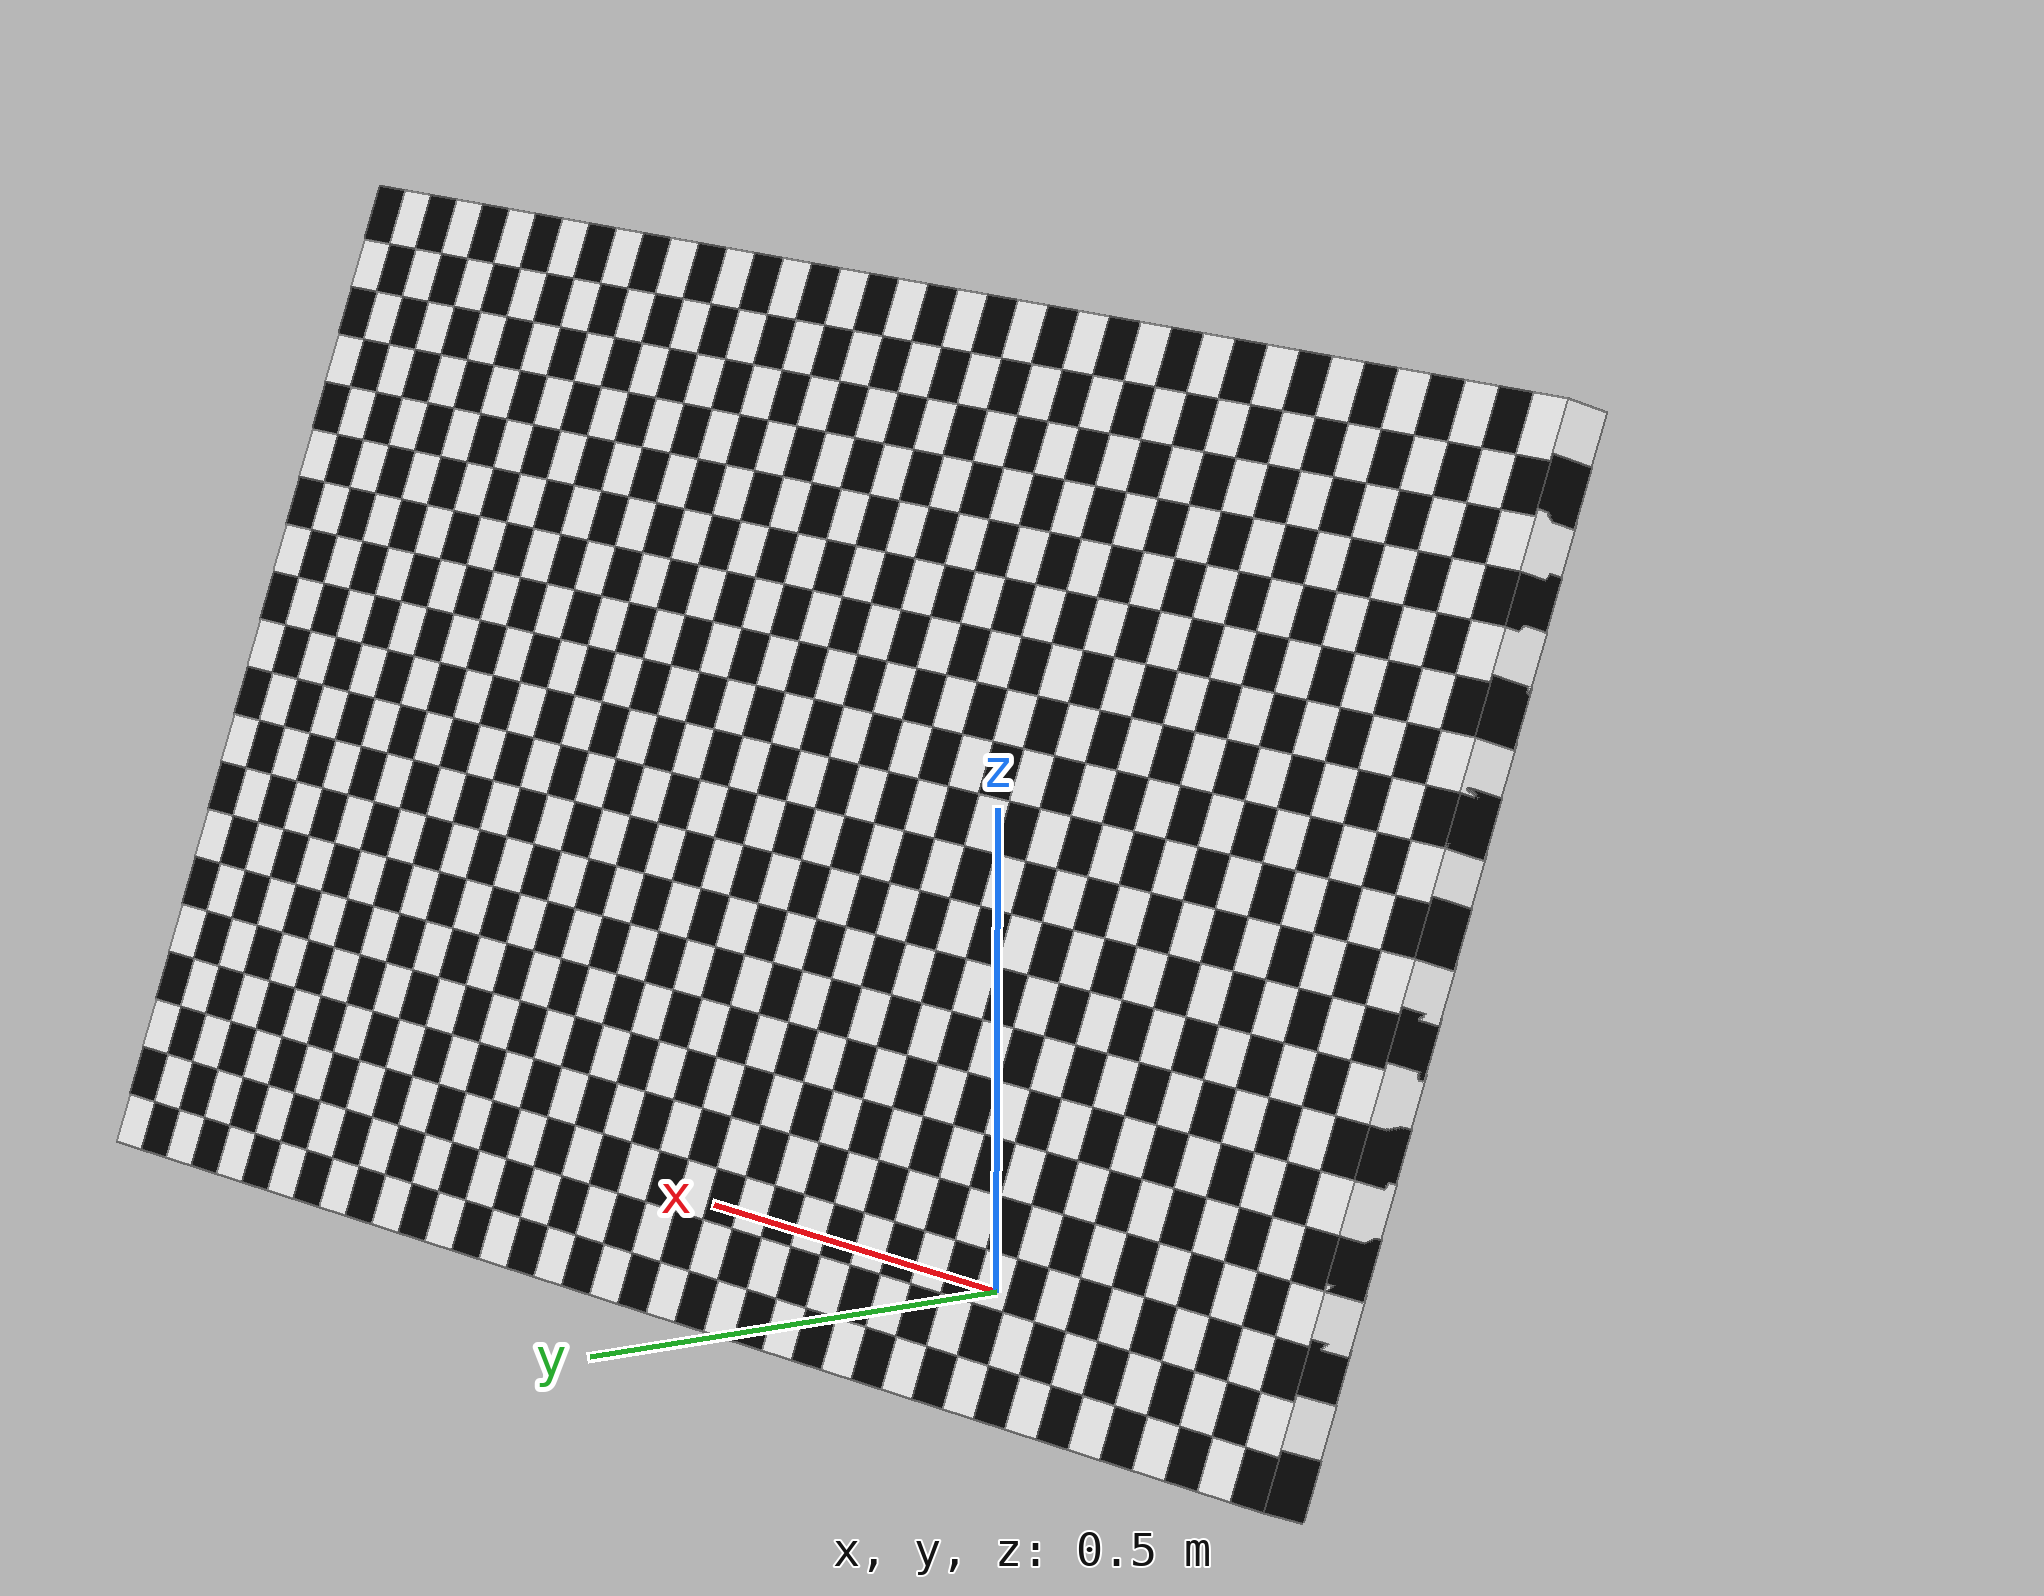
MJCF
<!-- This file was generated by angled_surface.py -->
<!-- It is not recommended to edit this file -->
<mujoco>
    <default>
        <geom density="100" friction=".5" rgba="1 .6 .8 1" />
    </default>
    <worldbody>
        <geom type="box" size=".025 .025 .03" pos="-0.95 0.057979856674331254 1.0" euler="20.0 0 0" rgba="1 1 1 1" />
<geom type="box" size=".025 .025 .03" pos="-0.8999999999999999 0.057979856674331254 1.0" euler="20.0 0 0" rgba="0 0 0 1" />
<geom type="box" size=".025 .025 .03" pos="-0.85 0.057979856674331254 1.0" euler="20.0 0 0" rgba="1 1 1 1" />
<geom type="box" size=".025 .025 .03" pos="-0.7999999999999999 0.057979856674331254 1.0" euler="20.0 0 0" rgba="0 0 0 1" />
<geom type="box" size=".025 .025 .03" pos="-0.75 0.057979856674331254 1.0" euler="20.0 0 0" rgba="1 1 1 1" />
<geom type="box" size=".025 .025 .03" pos="-0.7 0.057979856674331254 1.0" euler="20.0 0 0" rgba="0 0 0 1" />
<geom type="box" size=".025 .025 .03" pos="-0.6499999999999999 0.057979856674331254 1.0" euler="20.0 0 0" rgba="1 1 1 1" />
<geom type="box" size=".025 .025 .03" pos="-0.5999999999999999 0.057979856674331254 1.0" euler="20.0 0 0" rgba="0 0 0 1" />
<geom type="box" size=".025 .025 .03" pos="-0.5499999999999999 0.057979856674331254 1.0" euler="20.0 0 0" rgba="1 1 1 1" />
<geom type="box" size=".025 .025 .03" pos="-0.49999999999999994 0.057979856674331254 1.0" euler="20.0 0 0" rgba="0 0 0 1" />
<geom type="box" size=".025 .025 .03" pos="-0.44999999999999996 0.057979856674331254 1.0" euler="20.0 0 0" rgba="1 1 1 1" />
<geom type="box" size=".025 .025 .03" pos="-0.3999999999999999 0.057979856674331254 1.0" euler="20.0 0 0" rgba="0 0 0 1" />
<geom type="box" size=".025 .025 .03" pos="-0.34999999999999987 0.057979856674331254 1.0" euler="20.0 0 0" rgba="1 1 1 1" />
<geom type="box" size=".025 .025 .03" pos="-0.29999999999999993 0.057979856674331254 1.0" euler="20.0 0 0" rgba="0 0 0 1" />
<geom type="box" size=".025 .025 .03" pos="-0.2499999999999999 0.057979856674331254 1.0" euler="20.0 0 0" rgba="1 1 1 1" />
<geom type="box" size=".025 .025 .03" pos="-0.19999999999999996 0.057979856674331254 1.0" euler="20.0 0 0" rgba="0 0 0 1" />
<geom type="box" size=".025 .025 .03" pos="-0.1499999999999999 0.057979856674331254 1.0" euler="20.0 0 0" rgba="1 1 1 1" />
<geom type="box" size=".025 .025 .03" pos="-0.09999999999999987 0.057979856674331254 1.0" euler="20.0 0 0" rgba="0 0 0 1" />
<geom type="box" size=".025 .025 .03" pos="-0.04999999999999993 0.057979856674331254 1.0" euler="20.0 0 0" rgba="1 1 1 1" />
<geom type="box" size=".025 .025 .03" pos="1.1102230246251565e-16 0.057979856674331254 1.0" euler="20.0 0 0" rgba="0 0 0 1" />
<geom type="box" size=".025 .025 .03" pos="0.050000000000000044 0.057979856674331254 1.0" euler="20.0 0 0" rgba="1 1 1 1" />
<geom type="box" size=".025 .025 .03" pos="0.10000000000000009 0.057979856674331254 1.0" euler="20.0 0 0" rgba="0 0 0 1" />
<geom type="box" size=".025 .025 .03" pos="0.15000000000000013 0.057979856674331254 1.0" euler="20.0 0 0" rgba="1 1 1 1" />
<geom type="box" size=".025 .025 .03" pos="0.20000000000000018 0.057979856674331254 1.0" euler="20.0 0 0" rgba="0 0 0 1" />
<geom type="box" size=".025 .025 .03" pos="0.2500000000000002 0.057979856674331254 1.0" euler="20.0 0 0" rgba="1 1 1 1" />
<geom type="box" size=".025 .025 .03" pos="0.30000000000000004 0.057979856674331254 1.0" euler="20.0 0 0" rgba="0 0 0 1" />
<geom type="box" size=".025 .025 .03" pos="0.3500000000000001 0.057979856674331254 1.0" euler="20.0 0 0" rgba="1 1 1 1" />
<geom type="box" size=".025 .025 .03" pos="0.40000000000000013 0.057979856674331254 1.0" euler="20.0 0 0" rgba="0 0 0 1" />
<geom type="box" size=".025 .025 .03" pos="0.4500000000000002 0.057979856674331254 1.0" euler="20.0 0 0" rgba="1 1 1 1" />
<geom type="box" size=".025 .025 .03" pos="0.5000000000000002 0.057979856674331254 1.0" euler="20.0 0 0" rgba="0 0 0 1" />
<geom type="box" size=".025 .025 .03" pos="0.55 0.057979856674331254 1.0" euler="20.0 0 0" rgba="1 1 1 1" />
<geom type="box" size=".025 .025 .03" pos="0.6000000000000001 0.057979856674331254 1.0" euler="20.0 0 0" rgba="0 0 0 1" />
<geom type="box" size=".025 .025 .03" pos="0.6500000000000001 0.057979856674331254 1.0" euler="20.0 0 0" rgba="1 1 1 1" />
<geom type="box" size=".025 .025 .03" pos="0.7000000000000002 0.057979856674331254 1.0" euler="20.0 0 0" rgba="0 0 0 1" />
<geom type="box" size=".025 .025 .03" pos="0.7500000000000002 0.057979856674331254 1.0" euler="20.0 0 0" rgba="1 1 1 1" />
<geom type="box" size=".025 .025 .03" pos="0.8 0.057979856674331254 1.0" euler="20.0 0 0" rgba="0 0 0 1" />
<geom type="box" size=".025 .025 .03" pos="0.8500000000000001 0.057979856674331254 1.0" euler="20.0 0 0" rgba="1 1 1 1" />
<geom type="box" size=".025 .025 .03" pos="0.9000000000000001 0.057979856674331254 1.0" euler="20.0 0 0" rgba="0 0 0 1" />
<geom type="box" size=".025 .025 .03" pos="0.9500000000000002 0.057979856674331254 1.0" euler="20.0 0 0" rgba="1 1 1 1" />
<geom type="box" size=".025 .025 .03" pos="1.0000000000000002 0.057979856674331254 1.0" euler="20.0 0 0" rgba="0 0 0 1" />
<geom type="box" size=".025 .025 .03" pos="-0.95 0.07508086384061469 0.95" euler="20.0 0 0" rgba="0 0 0 1" />
<geom type="box" size=".025 .025 .03" pos="-0.8999999999999999 0.07508086384061469 0.95" euler="20.0 0 0" rgba="1 1 1 1" />
<geom type="box" size=".025 .025 .03" pos="-0.85 0.07508086384061469 0.95" euler="20.0 0 0" rgba="0 0 0 1" />
<geom type="box" size=".025 .025 .03" pos="-0.7999999999999999 0.07508086384061469 0.95" euler="20.0 0 0" rgba="1 1 1 1" />
<geom type="box" size=".025 .025 .03" pos="-0.75 0.07508086384061469 0.95" euler="20.0 0 0" rgba="0 0 0 1" />
<geom type="box" size=".025 .025 .03" pos="-0.7 0.07508086384061469 0.95" euler="20.0 0 0" rgba="1 1 1 1" />
<geom type="box" size=".025 .025 .03" pos="-0.6499999999999999 0.07508086384061469 0.95" euler="20.0 0 0" rgba="0 0 0 1" />
<geom type="box" size=".025 .025 .03" pos="-0.5999999999999999 0.07508086384061469 0.95" euler="20.0 0 0" rgba="1 1 1 1" />
<geom type="box" size=".025 .025 .03" pos="-0.5499999999999999 0.07508086384061469 0.95" euler="20.0 0 0" rgba="0 0 0 1" />
<geom type="box" size=".025 .025 .03" pos="-0.49999999999999994 0.07508086384061469 0.95" euler="20.0 0 0" rgba="1 1 1 1" />
<geom type="box" size=".025 .025 .03" pos="-0.44999999999999996 0.07508086384061469 0.95" euler="20.0 0 0" rgba="0 0 0 1" />
<geom type="box" size=".025 .025 .03" pos="-0.3999999999999999 0.07508086384061469 0.95" euler="20.0 0 0" rgba="1 1 1 1" />
<geom type="box" size=".025 .025 .03" pos="-0.34999999999999987 0.07508086384061469 0.95" euler="20.0 0 0" rgba="0 0 0 1" />
<geom type="box" size=".025 .025 .03" pos="-0.29999999999999993 0.07508086384061469 0.95" euler="20.0 0 0" rgba="1 1 1 1" />
<geom type="box" size=".025 .025 .03" pos="-0.2499999999999999 0.07508086384061469 0.95" euler="20.0 0 0" rgba="0 0 0 1" />
<geom type="box" size=".025 .025 .03" pos="-0.19999999999999996 0.07508086384061469 0.95" euler="20.0 0 0" rgba="1 1 1 1" />
<geom type="box" size=".025 .025 .03" pos="-0.1499999999999999 0.07508086384061469 0.95" euler="20.0 0 0" rgba="0 0 0 1" />
<geom type="box" size=".025 .025 .03" pos="-0.09999999999999987 0.07508086384061469 0.95" euler="20.0 0 0" rgba="1 1 1 1" />
<geom type="box" size=".025 .025 .03" pos="-0.04999999999999993 0.07508086384061469 0.95" euler="20.0 0 0" rgba="0 0 0 1" />
<geom type="box" size=".025 .025 .03" pos="1.1102230246251565e-16 0.07508086384061469 0.95" euler="20.0 0 0" rgba="1 1 1 1" />
<geom type="box" size=".025 .025 .03" pos="0.050000000000000044 0.07508086384061469 0.95" euler="20.0 0 0" rgba="0 0 0 1" />
<geom type="box" size=".025 .025 .03" pos="0.10000000000000009 0.07508086384061469 0.95" euler="20.0 0 0" rgba="1 1 1 1" />
<geom type="box" size=".025 .025 .03" pos="0.15000000000000013 0.07508086384061469 0.95" euler="20.0 0 0" rgba="0 0 0 1" />
<geom type="box" size=".025 .025 .03" pos="0.20000000000000018 0.07508086384061469 0.95" euler="20.0 0 0" rgba="1 1 1 1" />
<geom type="box" size=".025 .025 .03" pos="0.2500000000000002 0.07508086384061469 0.95" euler="20.0 0 0" rgba="0 0 0 1" />
<geom type="box" size=".025 .025 .03" pos="0.30000000000000004 0.07508086384061469 0.95" euler="20.0 0 0" rgba="1 1 1 1" />
<geom type="box" size=".025 .025 .03" pos="0.3500000000000001 0.07508086384061469 0.95" euler="20.0 0 0" rgba="0 0 0 1" />
<geom type="box" size=".025 .025 .03" pos="0.40000000000000013 0.07508086384061469 0.95" euler="20.0 0 0" rgba="1 1 1 1" />
<geom type="box" size=".025 .025 .03" pos="0.4500000000000002 0.07508086384061469 0.95" euler="20.0 0 0" rgba="0 0 0 1" />
<geom type="box" size=".025 .025 .03" pos="0.5000000000000002 0.07508086384061469 0.95" euler="20.0 0 0" rgba="1 1 1 1" />
<geom type="box" size=".025 .025 .03" pos="0.55 0.07508086384061469 0.95" euler="20.0 0 0" rgba="0 0 0 1" />
<geom type="box" size=".025 .025 .03" pos="0.6000000000000001 0.07508086384061469 0.95" euler="20.0 0 0" rgba="1 1 1 1" />
<geom type="box" size=".025 .025 .03" pos="0.6500000000000001 0.07508086384061469 0.95" euler="20.0 0 0" rgba="0 0 0 1" />
<geom type="box" size=".025 .025 .03" pos="0.7000000000000002 0.07508086384061469 0.95" euler="20.0 0 0" rgba="1 1 1 1" />
<geom type="box" size=".025 .025 .03" pos="0.7500000000000002 0.07508086384061469 0.95" euler="20.0 0 0" rgba="0 0 0 1" />
<geom type="box" size=".025 .025 .03" pos="0.8 0.07508086384061469 0.95" euler="20.0 0 0" rgba="1 1 1 1" />
<geom type="box" size=".025 .025 .03" pos="0.8500000000000001 0.07508086384061469 0.95" euler="20.0 0 0" rgba="0 0 0 1" />
<geom type="box" size=".025 .025 .03" pos="0.9000000000000001 0.07508086384061469 0.95" euler="20.0 0 0" rgba="1 1 1 1" />
<geom type="box" size=".025 .025 .03" pos="0.9500000000000002 0.07508086384061469 0.95" euler="20.0 0 0" rgba="0 0 0 1" />
<geom type="box" size=".025 .025 .03" pos="1.0000000000000002 0.07508086384061469 0.95" euler="20.0 0 0" rgba="1 1 1 1" />
<geom type="box" size=".025 .025 .03" pos="-0.95 0.09218187100689812 0.9" euler="20.0 0 0" rgba="1 1 1 1" />
<geom type="box" size=".025 .025 .03" pos="-0.8999999999999999 0.09218187100689812 0.9" euler="20.0 0 0" rgba="0 0 0 1" />
<geom type="box" size=".025 .025 .03" pos="-0.85 0.09218187100689812 0.9" euler="20.0 0 0" rgba="1 1 1 1" />
<geom type="box" size=".025 .025 .03" pos="-0.7999999999999999 0.09218187100689812 0.9" euler="20.0 0 0" rgba="0 0 0 1" />
<geom type="box" size=".025 .025 .03" pos="-0.75 0.09218187100689812 0.9" euler="20.0 0 0" rgba="1 1 1 1" />
<geom type="box" size=".025 .025 .03" pos="-0.7 0.09218187100689812 0.9" euler="20.0 0 0" rgba="0 0 0 1" />
<geom type="box" size=".025 .025 .03" pos="-0.6499999999999999 0.09218187100689812 0.9" euler="20.0 0 0" rgba="1 1 1 1" />
<geom type="box" size=".025 .025 .03" pos="-0.5999999999999999 0.09218187100689812 0.9" euler="20.0 0 0" rgba="0 0 0 1" />
<geom type="box" size=".025 .025 .03" pos="-0.5499999999999999 0.09218187100689812 0.9" euler="20.0 0 0" rgba="1 1 1 1" />
<geom type="box" size=".025 .025 .03" pos="-0.49999999999999994 0.09218187100689812 0.9" euler="20.0 0 0" rgba="0 0 0 1" />
<geom type="box" size=".025 .025 .03" pos="-0.44999999999999996 0.09218187100689812 0.9" euler="20.0 0 0" rgba="1 1 1 1" />
<geom type="box" size=".025 .025 .03" pos="-0.3999999999999999 0.09218187100689812 0.9" euler="20.0 0 0" rgba="0 0 0 1" />
<geom type="box" size=".025 .025 .03" pos="-0.34999999999999987 0.09218187100689812 0.9" euler="20.0 0 0" rgba="1 1 1 1" />
<geom type="box" size=".025 .025 .03" pos="-0.29999999999999993 0.09218187100689812 0.9" euler="20.0 0 0" rgba="0 0 0 1" />
<geom type="box" size=".025 .025 .03" pos="-0.2499999999999999 0.09218187100689812 0.9" euler="20.0 0 0" rgba="1 1 1 1" />
<geom type="box" size=".025 .025 .03" pos="-0.19999999999999996 0.09218187100689812 0.9" euler="20.0 0 0" rgba="0 0 0 1" />
<geom type="box" size=".025 .025 .03" pos="-0.1499999999999999 0.09218187100689812 0.9" euler="20.0 0 0" rgba="1 1 1 1" />
<geom type="box" size=".025 .025 .03" pos="-0.09999999999999987 0.09218187100689812 0.9" euler="20.0 0 0" rgba="0 0 0 1" />
<geom type="box" size=".025 .025 .03" pos="-0.04999999999999993 0.09218187100689812 0.9" euler="20.0 0 0" rgba="1 1 1 1" />
<geom type="box" size=".025 .025 .03" pos="1.1102230246251565e-16 0.09218187100689812 0.9" euler="20.0 0 0" rgba="0 0 0 1" />
<geom type="box" size=".025 .025 .03" pos="0.050000000000000044 0.09218187100689812 0.9" euler="20.0 0 0" rgba="1 1 1 1" />
<geom type="box" size=".025 .025 .03" pos="0.10000000000000009 0.09218187100689812 0.9" euler="20.0 0 0" rgba="0 0 0 1" />
<geom type="box" size=".025 .025 .03" pos="0.15000000000000013 0.09218187100689812 0.9" euler="20.0 0 0" rgba="1 1 1 1" />
<geom type="box" size=".025 .025 .03" pos="0.20000000000000018 0.09218187100689812 0.9" euler="20.0 0 0" rgba="0 0 0 1" />
<geom type="box" size=".025 .025 .03" pos="0.2500000000000002 0.09218187100689812 0.9" euler="20.0 0 0" rgba="1 1 1 1" />
<geom type="box" size=".025 .025 .03" pos="0.30000000000000004 0.09218187100689812 0.9" euler="20.0 0 0" rgba="0 0 0 1" />
<geom type="box" size=".025 .025 .03" pos="0.3500000000000001 0.09218187100689812 0.9" euler="20.0 0 0" rgba="1 1 1 1" />
<geom type="box" size=".025 .025 .03" pos="0.40000000000000013 0.09218187100689812 0.9" euler="20.0 0 0" rgba="0 0 0 1" />
<geom type="box" size=".025 .025 .03" pos="0.4500000000000002 0.09218187100689812 0.9" euler="20.0 0 0" rgba="1 1 1 1" />
<geom type="box" size=".025 .025 .03" pos="0.5000000000000002 0.09218187100689812 0.9" euler="20.0 0 0" rgba="0 0 0 1" />
<geom type="box" size=".025 .025 .03" pos="0.55 0.09218187100689812 0.9" euler="20.0 0 0" rgba="1 1 1 1" />
<geom type="box" size=".025 .025 .03" pos="0.6000000000000001 0.09218187100689812 0.9" euler="20.0 0 0" rgba="0 0 0 1" />
<geom type="box" size=".025 .025 .03" pos="0.6500000000000001 0.09218187100689812 0.9" euler="20.0 0 0" rgba="1 1 1 1" />
<geom type="box" size=".025 .025 .03" pos="0.7000000000000002 0.09218187100689812 0.9" euler="20.0 0 0" rgba="0 0 0 1" />
<geom type="box" size=".025 .025 .03" pos="0.7500000000000002 0.09218187100689812 0.9" euler="20.0 0 0" rgba="1 1 1 1" />
<geom type="box" size=".025 .025 .03" pos="0.8 0.09218187100689812 0.9" euler="20.0 0 0" rgba="0 0 0 1" />
<geom type="box" size=".025 .025 .03" pos="0.8500000000000001 0.09218187100689812 0.9" euler="20.0 0 0" rgba="1 1 1 1" />
<geom type="box" size=".025 .025 .03" pos="0.9000000000000001 0.09218187100689812 0.9" euler="20.0 0 0" rgba="0 0 0 1" />
<geom type="box" size=".025 .025 .03" pos="0.9500000000000002 0.09218187100689812 0.9" euler="20.0 0 0" rgba="1 1 1 1" />
<geom type="box" size=".025 .025 .03" pos="1.0000000000000002 0.09218187100689812 0.9" euler="20.0 0 0" rgba="0 0 0 1" />
<geom type="box" size=".025 .025 .03" pos="-0.95 0.10928287817318155 0.85" euler="20.0 0 0" rgba="0 0 0 1" />
<geom type="box" size=".025 .025 .03" pos="-0.8999999999999999 0.10928287817318155 0.85" euler="20.0 0 0" rgba="1 1 1 1" />
<geom type="box" size=".025 .025 .03" pos="-0.85 0.10928287817318155 0.85" euler="20.0 0 0" rgba="0 0 0 1" />
<geom type="box" size=".025 .025 .03" pos="-0.7999999999999999 0.10928287817318155 0.85" euler="20.0 0 0" rgba="1 1 1 1" />
<geom type="box" size=".025 .025 .03" pos="-0.75 0.10928287817318155 0.85" euler="20.0 0 0" rgba="0 0 0 1" />
<geom type="box" size=".025 .025 .03" pos="-0.7 0.10928287817318155 0.85" euler="20.0 0 0" rgba="1 1 1 1" />
<geom type="box" size=".025 .025 .03" pos="-0.6499999999999999 0.10928287817318155 0.85" euler="20.0 0 0" rgba="0 0 0 1" />
<geom type="box" size=".025 .025 .03" pos="-0.5999999999999999 0.10928287817318155 0.85" euler="20.0 0 0" rgba="1 1 1 1" />
<geom type="box" size=".025 .025 .03" pos="-0.5499999999999999 0.10928287817318155 0.85" euler="20.0 0 0" rgba="0 0 0 1" />
<geom type="box" size=".025 .025 .03" pos="-0.49999999999999994 0.10928287817318155 0.85" euler="20.0 0 0" rgba="1 1 1 1" />
<geom type="box" size=".025 .025 .03" pos="-0.44999999999999996 0.10928287817318155 0.85" euler="20.0 0 0" rgba="0 0 0 1" />
<geom type="box" size=".025 .025 .03" pos="-0.3999999999999999 0.10928287817318155 0.85" euler="20.0 0 0" rgba="1 1 1 1" />
<geom type="box" size=".025 .025 .03" pos="-0.34999999999999987 0.10928287817318155 0.85" euler="20.0 0 0" rgba="0 0 0 1" />
<geom type="box" size=".025 .025 .03" pos="-0.29999999999999993 0.10928287817318155 0.85" euler="20.0 0 0" rgba="1 1 1 1" />
<geom type="box" size=".025 .025 .03" pos="-0.2499999999999999 0.10928287817318155 0.85" euler="20.0 0 0" rgba="0 0 0 1" />
<geom type="box" size=".025 .025 .03" pos="-0.19999999999999996 0.10928287817318155 0.85" euler="20.0 0 0" rgba="1 1 1 1" />
<geom type="box" size=".025 .025 .03" pos="-0.1499999999999999 0.10928287817318155 0.85" euler="20.0 0 0" rgba="0 0 0 1" />
<geom type="box" size=".025 .025 .03" pos="-0.09999999999999987 0.10928287817318155 0.85" euler="20.0 0 0" rgba="1 1 1 1" />
<geom type="box" size=".025 .025 .03" pos="-0.04999999999999993 0.10928287817318155 0.85" euler="20.0 0 0" rgba="0 0 0 1" />
<geom type="box" size=".025 .025 .03" pos="1.1102230246251565e-16 0.10928287817318155 0.85" euler="20.0 0 0" rgba="1 1 1 1" />
<geom type="box" size=".025 .025 .03" pos="0.050000000000000044 0.10928287817318155 0.85" euler="20.0 0 0" rgba="0 0 0 1" />
<geom type="box" size=".025 .025 .03" pos="0.10000000000000009 0.10928287817318155 0.85" euler="20.0 0 0" rgba="1 1 1 1" />
<geom type="box" size=".025 .025 .03" pos="0.15000000000000013 0.10928287817318155 0.85" euler="20.0 0 0" rgba="0 0 0 1" />
<geom type="box" size=".025 .025 .03" pos="0.20000000000000018 0.10928287817318155 0.85" euler="20.0 0 0" rgba="1 1 1 1" />
<geom type="box" size=".025 .025 .03" pos="0.2500000000000002 0.10928287817318155 0.85" euler="20.0 0 0" rgba="0 0 0 1" />
<geom type="box" size=".025 .025 .03" pos="0.30000000000000004 0.10928287817318155 0.85" euler="20.0 0 0" rgba="1 1 1 1" />
<geom type="box" size=".025 .025 .03" pos="0.3500000000000001 0.10928287817318155 0.85" euler="20.0 0 0" rgba="0 0 0 1" />
<geom type="box" size=".025 .025 .03" pos="0.40000000000000013 0.10928287817318155 0.85" euler="20.0 0 0" rgba="1 1 1 1" />
<geom type="box" size=".025 .025 .03" pos="0.4500000000000002 0.10928287817318155 0.85" euler="20.0 0 0" rgba="0 0 0 1" />
<geom type="box" size=".025 .025 .03" pos="0.5000000000000002 0.10928287817318155 0.85" euler="20.0 0 0" rgba="1 1 1 1" />
<geom type="box" size=".025 .025 .03" pos="0.55 0.10928287817318155 0.85" euler="20.0 0 0" rgba="0 0 0 1" />
<geom type="box" size=".025 .025 .03" pos="0.6000000000000001 0.10928287817318155 0.85" euler="20.0 0 0" rgba="1 1 1 1" />
<geom type="box" size=".025 .025 .03" pos="0.6500000000000001 0.10928287817318155 0.85" euler="20.0 0 0" rgba="0 0 0 1" />
<geom type="box" size=".025 .025 .03" pos="0.7000000000000002 0.10928287817318155 0.85" euler="20.0 0 0" rgba="1 1 1 1" />
<geom type="box" size=".025 .025 .03" pos="0.7500000000000002 0.10928287817318155 0.85" euler="20.0 0 0" rgba="0 0 0 1" />
<geom type="box" size=".025 .025 .03" pos="0.8 0.10928287817318155 0.85" euler="20.0 0 0" rgba="1 1 1 1" />
<geom type="box" size=".025 .025 .03" pos="0.8500000000000001 0.10928287817318155 0.85" euler="20.0 0 0" rgba="0 0 0 1" />
<geom type="box" size=".025 .025 .03" pos="0.9000000000000001 0.10928287817318155 0.85" euler="20.0 0 0" rgba="1 1 1 1" />
<geom type="box" size=".025 .025 .03" pos="0.9500000000000002 0.10928287817318155 0.85" euler="20.0 0 0" rgba="0 0 0 1" />
<geom type="box" size=".025 .025 .03" pos="1.0000000000000002 0.10928287817318155 0.85" euler="20.0 0 0" rgba="1 1 1 1" />
<geom type="box" size=".025 .025 .03" pos="-0.95 0.12638388533946499 0.8" euler="20.0 0 0" rgba="1 1 1 1" />
<geom type="box" size=".025 .025 .03" pos="-0.8999999999999999 0.12638388533946499 0.8" euler="20.0 0 0" rgba="0 0 0 1" />
<geom type="box" size=".025 .025 .03" pos="-0.85 0.12638388533946499 0.8" euler="20.0 0 0" rgba="1 1 1 1" />
<geom type="box" size=".025 .025 .03" pos="-0.7999999999999999 0.12638388533946499 0.8" euler="20.0 0 0" rgba="0 0 0 1" />
<geom type="box" size=".025 .025 .03" pos="-0.75 0.12638388533946499 0.8" euler="20.0 0 0" rgba="1 1 1 1" />
<geom type="box" size=".025 .025 .03" pos="-0.7 0.12638388533946499 0.8" euler="20.0 0 0" rgba="0 0 0 1" />
<geom type="box" size=".025 .025 .03" pos="-0.6499999999999999 0.12638388533946499 0.8" euler="20.0 0 0" rgba="1 1 1 1" />
<geom type="box" size=".025 .025 .03" pos="-0.5999999999999999 0.12638388533946499 0.8" euler="20.0 0 0" rgba="0 0 0 1" />
<geom type="box" size=".025 .025 .03" pos="-0.5499999999999999 0.12638388533946499 0.8" euler="20.0 0 0" rgba="1 1 1 1" />
<geom type="box" size=".025 .025 .03" pos="-0.49999999999999994 0.12638388533946499 0.8" euler="20.0 0 0" rgba="0 0 0 1" />
<geom type="box" size=".025 .025 .03" pos="-0.44999999999999996 0.12638388533946499 0.8" euler="20.0 0 0" rgba="1 1 1 1" />
<geom type="box" size=".025 .025 .03" pos="-0.3999999999999999 0.12638388533946499 0.8" euler="20.0 0 0" rgba="0 0 0 1" />
<geom type="box" size=".025 .025 .03" pos="-0.34999999999999987 0.12638388533946499 0.8" euler="20.0 0 0" rgba="1 1 1 1" />
<geom type="box" size=".025 .025 .03" pos="-0.29999999999999993 0.12638388533946499 0.8" euler="20.0 0 0" rgba="0 0 0 1" />
<geom type="box" size=".025 .025 .03" pos="-0.2499999999999999 0.12638388533946499 0.8" euler="20.0 0 0" rgba="1 1 1 1" />
<geom type="box" size=".025 .025 .03" pos="-0.19999999999999996 0.12638388533946499 0.8" euler="20.0 0 0" rgba="0 0 0 1" />
<geom type="box" size=".025 .025 .03" pos="-0.1499999999999999 0.12638388533946499 0.8" euler="20.0 0 0" rgba="1 1 1 1" />
<geom type="box" size=".025 .025 .03" pos="-0.09999999999999987 0.12638388533946499 0.8" euler="20.0 0 0" rgba="0 0 0 1" />
<geom type="box" size=".025 .025 .03" pos="-0.04999999999999993 0.12638388533946499 0.8" euler="20.0 0 0" rgba="1 1 1 1" />
<geom type="box" size=".025 .025 .03" pos="1.1102230246251565e-16 0.12638388533946499 0.8" euler="20.0 0 0" rgba="0 0 0 1" />
<geom type="box" size=".025 .025 .03" pos="0.050000000000000044 0.12638388533946499 0.8" euler="20.0 0 0" rgba="1 1 1 1" />
<geom type="box" size=".025 .025 .03" pos="0.10000000000000009 0.12638388533946499 0.8" euler="20.0 0 0" rgba="0 0 0 1" />
<geom type="box" size=".025 .025 .03" pos="0.15000000000000013 0.12638388533946499 0.8" euler="20.0 0 0" rgba="1 1 1 1" />
<geom type="box" size=".025 .025 .03" pos="0.20000000000000018 0.12638388533946499 0.8" euler="20.0 0 0" rgba="0 0 0 1" />
<geom type="box" size=".025 .025 .03" pos="0.2500000000000002 0.12638388533946499 0.8" euler="20.0 0 0" rgba="1 1 1 1" />
<geom type="box" size=".025 .025 .03" pos="0.30000000000000004 0.12638388533946499 0.8" euler="20.0 0 0" rgba="0 0 0 1" />
<geom type="box" size=".025 .025 .03" pos="0.3500000000000001 0.12638388533946499 0.8" euler="20.0 0 0" rgba="1 1 1 1" />
<geom type="box" size=".025 .025 .03" pos="0.40000000000000013 0.12638388533946499 0.8" euler="20.0 0 0" rgba="0 0 0 1" />
<geom type="box" size=".025 .025 .03" pos="0.4500000000000002 0.12638388533946499 0.8" euler="20.0 0 0" rgba="1 1 1 1" />
<geom type="box" size=".025 .025 .03" pos="0.5000000000000002 0.12638388533946499 0.8" euler="20.0 0 0" rgba="0 0 0 1" />
<geom type="box" size=".025 .025 .03" pos="0.55 0.12638388533946499 0.8" euler="20.0 0 0" rgba="1 1 1 1" />
<geom type="box" size=".025 .025 .03" pos="0.6000000000000001 0.12638388533946499 0.8" euler="20.0 0 0" rgba="0 0 0 1" />
<geom type="box" size=".025 .025 .03" pos="0.6500000000000001 0.12638388533946499 0.8" euler="20.0 0 0" rgba="1 1 1 1" />
<geom type="box" size=".025 .025 .03" pos="0.7000000000000002 0.12638388533946499 0.8" euler="20.0 0 0" rgba="0 0 0 1" />
<geom type="box" size=".025 .025 .03" pos="0.7500000000000002 0.12638388533946499 0.8" euler="20.0 0 0" rgba="1 1 1 1" />
<geom type="box" size=".025 .025 .03" pos="0.8 0.12638388533946499 0.8" euler="20.0 0 0" rgba="0 0 0 1" />
<geom type="box" size=".025 .025 .03" pos="0.8500000000000001 0.12638388533946499 0.8" euler="20.0 0 0" rgba="1 1 1 1" />
<geom type="box" size=".025 .025 .03" pos="0.9000000000000001 0.12638388533946499 0.8" euler="20.0 0 0" rgba="0 0 0 1" />
<geom type="box" size=".025 .025 .03" pos="0.9500000000000002 0.12638388533946499 0.8" euler="20.0 0 0" rgba="1 1 1 1" />
<geom type="box" size=".025 .025 .03" pos="1.0000000000000002 0.12638388533946499 0.8" euler="20.0 0 0" rgba="0 0 0 1" />
<geom type="box" size=".025 .025 .03" pos="-0.95 0.14348489250574842 0.75" euler="20.0 0 0" rgba="0 0 0 1" />
<geom type="box" size=".025 .025 .03" pos="-0.8999999999999999 0.14348489250574842 0.75" euler="20.0 0 0" rgba="1 1 1 1" />
<geom type="box" size=".025 .025 .03" pos="-0.85 0.14348489250574842 0.75" euler="20.0 0 0" rgba="0 0 0 1" />
<geom type="box" size=".025 .025 .03" pos="-0.7999999999999999 0.14348489250574842 0.75" euler="20.0 0 0" rgba="1 1 1 1" />
<geom type="box" size=".025 .025 .03" pos="-0.75 0.14348489250574842 0.75" euler="20.0 0 0" rgba="0 0 0 1" />
<geom type="box" size=".025 .025 .03" pos="-0.7 0.14348489250574842 0.75" euler="20.0 0 0" rgba="1 1 1 1" />
<geom type="box" size=".025 .025 .03" pos="-0.6499999999999999 0.14348489250574842 0.75" euler="20.0 0 0" rgba="0 0 0 1" />
<geom type="box" size=".025 .025 .03" pos="-0.5999999999999999 0.14348489250574842 0.75" euler="20.0 0 0" rgba="1 1 1 1" />
<geom type="box" size=".025 .025 .03" pos="-0.5499999999999999 0.14348489250574842 0.75" euler="20.0 0 0" rgba="0 0 0 1" />
<geom type="box" size=".025 .025 .03" pos="-0.49999999999999994 0.14348489250574842 0.75" euler="20.0 0 0" rgba="1 1 1 1" />
<geom type="box" size=".025 .025 .03" pos="-0.44999999999999996 0.14348489250574842 0.75" euler="20.0 0 0" rgba="0 0 0 1" />
<geom type="box" size=".025 .025 .03" pos="-0.3999999999999999 0.14348489250574842 0.75" euler="20.0 0 0" rgba="1 1 1 1" />
<geom type="box" size=".025 .025 .03" pos="-0.34999999999999987 0.14348489250574842 0.75" euler="20.0 0 0" rgba="0 0 0 1" />
<geom type="box" size=".025 .025 .03" pos="-0.29999999999999993 0.14348489250574842 0.75" euler="20.0 0 0" rgba="1 1 1 1" />
<geom type="box" size=".025 .025 .03" pos="-0.2499999999999999 0.14348489250574842 0.75" euler="20.0 0 0" rgba="0 0 0 1" />
<geom type="box" size=".025 .025 .03" pos="-0.19999999999999996 0.14348489250574842 0.75" euler="20.0 0 0" rgba="1 1 1 1" />
<geom type="box" size=".025 .025 .03" pos="-0.1499999999999999 0.14348489250574842 0.75" euler="20.0 0 0" rgba="0 0 0 1" />
<geom type="box" size=".025 .025 .03" pos="-0.09999999999999987 0.14348489250574842 0.75" euler="20.0 0 0" rgba="1 1 1 1" />
<geom type="box" size=".025 .025 .03" pos="-0.04999999999999993 0.14348489250574842 0.75" euler="20.0 0 0" rgba="0 0 0 1" />
<geom type="box" size=".025 .025 .03" pos="1.1102230246251565e-16 0.14348489250574842 0.75" euler="20.0 0 0" rgba="1 1 1 1" />
<geom type="box" size=".025 .025 .03" pos="0.050000000000000044 0.14348489250574842 0.75" euler="20.0 0 0" rgba="0 0 0 1" />
<geom type="box" size=".025 .025 .03" pos="0.10000000000000009 0.14348489250574842 0.75" euler="20.0 0 0" rgba="1 1 1 1" />
<geom type="box" size=".025 .025 .03" pos="0.15000000000000013 0.14348489250574842 0.75" euler="20.0 0 0" rgba="0 0 0 1" />
<geom type="box" size=".025 .025 .03" pos="0.20000000000000018 0.14348489250574842 0.75" euler="20.0 0 0" rgba="1 1 1 1" />
<geom type="box" size=".025 .025 .03" pos="0.2500000000000002 0.14348489250574842 0.75" euler="20.0 0 0" rgba="0 0 0 1" />
<geom type="box" size=".025 .025 .03" pos="0.30000000000000004 0.14348489250574842 0.75" euler="20.0 0 0" rgba="1 1 1 1" />
<geom type="box" size=".025 .025 .03" pos="0.3500000000000001 0.14348489250574842 0.75" euler="20.0 0 0" rgba="0 0 0 1" />
<geom type="box" size=".025 .025 .03" pos="0.40000000000000013 0.14348489250574842 0.75" euler="20.0 0 0" rgba="1 1 1 1" />
<geom type="box" size=".025 .025 .03" pos="0.4500000000000002 0.14348489250574842 0.75" euler="20.0 0 0" rgba="0 0 0 1" />
<geom type="box" size=".025 .025 .03" pos="0.5000000000000002 0.14348489250574842 0.75" euler="20.0 0 0" rgba="1 1 1 1" />
<geom type="box" size=".025 .025 .03" pos="0.55 0.14348489250574842 0.75" euler="20.0 0 0" rgba="0 0 0 1" />
<geom type="box" size=".025 .025 .03" pos="0.6000000000000001 0.14348489250574842 0.75" euler="20.0 0 0" rgba="1 1 1 1" />
<geom type="box" size=".025 .025 .03" pos="0.6500000000000001 0.14348489250574842 0.75" euler="20.0 0 0" rgba="0 0 0 1" />
<geom type="box" size=".025 .025 .03" pos="0.7000000000000002 0.14348489250574842 0.75" euler="20.0 0 0" rgba="1 1 1 1" />
<geom type="box" size=".025 .025 .03" pos="0.7500000000000002 0.14348489250574842 0.75" euler="20.0 0 0" rgba="0 0 0 1" />
<geom type="box" size=".025 .025 .03" pos="0.8 0.14348489250574842 0.75" euler="20.0 0 0" rgba="1 1 1 1" />
<geom type="box" size=".025 .025 .03" pos="0.8500000000000001 0.14348489250574842 0.75" euler="20.0 0 0" rgba="0 0 0 1" />
<geom type="box" size=".025 .025 .03" pos="0.9000000000000001 0.14348489250574842 0.75" euler="20.0 0 0" rgba="1 1 1 1" />
<geom type="box" size=".025 .025 .03" pos="0.9500000000000002 0.14348489250574842 0.75" euler="20.0 0 0" rgba="0 0 0 1" />
<geom type="box" size=".025 .025 .03" pos="1.0000000000000002 0.14348489250574842 0.75" euler="20.0 0 0" rgba="1 1 1 1" />
<geom type="box" size=".025 .025 .03" pos="-0.95 0.1605858996720319 0.7" euler="20.0 0 0" rgba="1 1 1 1" />
<geom type="box" size=".025 .025 .03" pos="-0.8999999999999999 0.1605858996720319 0.7" euler="20.0 0 0" rgba="0 0 0 1" />
<geom type="box" size=".025 .025 .03" pos="-0.85 0.1605858996720319 0.7" euler="20.0 0 0" rgba="1 1 1 1" />
<geom type="box" size=".025 .025 .03" pos="-0.7999999999999999 0.1605858996720319 0.7" euler="20.0 0 0" rgba="0 0 0 1" />
<geom type="box" size=".025 .025 .03" pos="-0.75 0.1605858996720319 0.7" euler="20.0 0 0" rgba="1 1 1 1" />
<geom type="box" size=".025 .025 .03" pos="-0.7 0.1605858996720319 0.7" euler="20.0 0 0" rgba="0 0 0 1" />
<geom type="box" size=".025 .025 .03" pos="-0.6499999999999999 0.1605858996720319 0.7" euler="20.0 0 0" rgba="1 1 1 1" />
<geom type="box" size=".025 .025 .03" pos="-0.5999999999999999 0.1605858996720319 0.7" euler="20.0 0 0" rgba="0 0 0 1" />
<geom type="box" size=".025 .025 .03" pos="-0.5499999999999999 0.1605858996720319 0.7" euler="20.0 0 0" rgba="1 1 1 1" />
<geom type="box" size=".025 .025 .03" pos="-0.49999999999999994 0.1605858996720319 0.7" euler="20.0 0 0" rgba="0 0 0 1" />
<geom type="box" size=".025 .025 .03" pos="-0.44999999999999996 0.1605858996720319 0.7" euler="20.0 0 0" rgba="1 1 1 1" />
<geom type="box" size=".025 .025 .03" pos="-0.3999999999999999 0.1605858996720319 0.7" euler="20.0 0 0" rgba="0 0 0 1" />
<geom type="box" size=".025 .025 .03" pos="-0.34999999999999987 0.1605858996720319 0.7" euler="20.0 0 0" rgba="1 1 1 1" />
<geom type="box" size=".025 .025 .03" pos="-0.29999999999999993 0.1605858996720319 0.7" euler="20.0 0 0" rgba="0 0 0 1" />
<geom type="box" size=".025 .025 .03" pos="-0.2499999999999999 0.1605858996720319 0.7" euler="20.0 0 0" rgba="1 1 1 1" />
<geom type="box" size=".025 .025 .03" pos="-0.19999999999999996 0.1605858996720319 0.7" euler="20.0 0 0" rgba="0 0 0 1" />
<geom type="box" size=".025 .025 .03" pos="-0.1499999999999999 0.1605858996720319 0.7" euler="20.0 0 0" rgba="1 1 1 1" />
<geom type="box" size=".025 .025 .03" pos="-0.09999999999999987 0.1605858996720319 0.7" euler="20.0 0 0" rgba="0 0 0 1" />
<geom type="box" size=".025 .025 .03" pos="-0.04999999999999993 0.1605858996720319 0.7" euler="20.0 0 0" rgba="1 1 1 1" />
<geom type="box" size=".025 .025 .03" pos="1.1102230246251565e-16 0.1605858996720319 0.7" euler="20.0 0 0" rgba="0 0 0 1" />
<geom type="box" size=".025 .025 .03" pos="0.050000000000000044 0.1605858996720319 0.7" euler="20.0 0 0" rgba="1 1 1 1" />
<geom type="box" size=".025 .025 .03" pos="0.10000000000000009 0.1605858996720319 0.7" euler="20.0 0 0" rgba="0 0 0 1" />
<geom type="box" size=".025 .025 .03" pos="0.15000000000000013 0.1605858996720319 0.7" euler="20.0 0 0" rgba="1 1 1 1" />
<geom type="box" size=".025 .025 .03" pos="0.20000000000000018 0.1605858996720319 0.7" euler="20.0 0 0" rgba="0 0 0 1" />
<geom type="box" size=".025 .025 .03" pos="0.2500000000000002 0.1605858996720319 0.7" euler="20.0 0 0" rgba="1 1 1 1" />
<geom type="box" size=".025 .025 .03" pos="0.30000000000000004 0.1605858996720319 0.7" euler="20.0 0 0" rgba="0 0 0 1" />
<geom type="box" size=".025 .025 .03" pos="0.3500000000000001 0.1605858996720319 0.7" euler="20.0 0 0" rgba="1 1 1 1" />
<geom type="box" size=".025 .025 .03" pos="0.40000000000000013 0.1605858996720319 0.7" euler="20.0 0 0" rgba="0 0 0 1" />
<geom type="box" size=".025 .025 .03" pos="0.4500000000000002 0.1605858996720319 0.7" euler="20.0 0 0" rgba="1 1 1 1" />
<geom type="box" size=".025 .025 .03" pos="0.5000000000000002 0.1605858996720319 0.7" euler="20.0 0 0" rgba="0 0 0 1" />
<geom type="box" size=".025 .025 .03" pos="0.55 0.1605858996720319 0.7" euler="20.0 0 0" rgba="1 1 1 1" />
<geom type="box" size=".025 .025 .03" pos="0.6000000000000001 0.1605858996720319 0.7" euler="20.0 0 0" rgba="0 0 0 1" />
<geom type="box" size=".025 .025 .03" pos="0.6500000000000001 0.1605858996720319 0.7" euler="20.0 0 0" rgba="1 1 1 1" />
<geom type="box" size=".025 .025 .03" pos="0.7000000000000002 0.1605858996720319 0.7" euler="20.0 0 0" rgba="0 0 0 1" />
<geom type="box" size=".025 .025 .03" pos="0.7500000000000002 0.1605858996720319 0.7" euler="20.0 0 0" rgba="1 1 1 1" />
<geom type="box" size=".025 .025 .03" pos="0.8 0.1605858996720319 0.7" euler="20.0 0 0" rgba="0 0 0 1" />
<geom type="box" size=".025 .025 .03" pos="0.8500000000000001 0.1605858996720319 0.7" euler="20.0 0 0" rgba="1 1 1 1" />
<geom type="box" size=".025 .025 .03" pos="0.9000000000000001 0.1605858996720319 0.7" euler="20.0 0 0" rgba="0 0 0 1" />
<geom type="box" size=".025 .025 .03" pos="0.9500000000000002 0.1605858996720319 0.7" euler="20.0 0 0" rgba="1 1 1 1" />
<geom type="box" size=".025 .025 .03" pos="1.0000000000000002 0.1605858996720319 0.7" euler="20.0 0 0" rgba="0 0 0 1" />
<geom type="box" size=".025 .025 .03" pos="-0.95 0.17768690683831528 0.6499999999999999" euler="20.0 0 0" rgba="0 0 0 1" />
<geom type="box" size=".025 .025 .03" pos="-0.8999999999999999 0.17768690683831528 0.6499999999999999" euler="20.0 0 0" rgba="1 1 1 1" />
<geom type="box" size=".025 .025 .03" pos="-0.85 0.17768690683831528 0.6499999999999999" euler="20.0 0 0" rgba="0 0 0 1" />
<geom type="box" size=".025 .025 .03" pos="-0.7999999999999999 0.17768690683831528 0.6499999999999999" euler="20.0 0 0" rgba="1 1 1 1" />
<geom type="box" size=".025 .025 .03" pos="-0.75 0.17768690683831528 0.6499999999999999" euler="20.0 0 0" rgba="0 0 0 1" />
<geom type="box" size=".025 .025 .03" pos="-0.7 0.17768690683831528 0.6499999999999999" euler="20.0 0 0" rgba="1 1 1 1" />
<geom type="box" size=".025 .025 .03" pos="-0.6499999999999999 0.17768690683831528 0.6499999999999999" euler="20.0 0 0" rgba="0 0 0 1" />
<geom type="box" size=".025 .025 .03" pos="-0.5999999999999999 0.17768690683831528 0.6499999999999999" euler="20.0 0 0" rgba="1 1 1 1" />
<geom type="box" size=".025 .025 .03" pos="-0.5499999999999999 0.17768690683831528 0.6499999999999999" euler="20.0 0 0" rgba="0 0 0 1" />
<geom type="box" size=".025 .025 .03" pos="-0.49999999999999994 0.17768690683831528 0.6499999999999999" euler="20.0 0 0" rgba="1 1 1 1" />
<geom type="box" size=".025 .025 .03" pos="-0.44999999999999996 0.17768690683831528 0.6499999999999999" euler="20.0 0 0" rgba="0 0 0 1" />
<geom type="box" size=".025 .025 .03" pos="-0.3999999999999999 0.17768690683831528 0.6499999999999999" euler="20.0 0 0" rgba="1 1 1 1" />
<geom type="box" size=".025 .025 .03" pos="-0.34999999999999987 0.17768690683831528 0.6499999999999999" euler="20.0 0 0" rgba="0 0 0 1" />
<geom type="box" size=".025 .025 .03" pos="-0.29999999999999993 0.17768690683831528 0.6499999999999999" euler="20.0 0 0" rgba="1 1 1 1" />
<geom type="box" size=".025 .025 .03" pos="-0.2499999999999999 0.17768690683831528 0.6499999999999999" euler="20.0 0 0" rgba="0 0 0 1" />
<geom type="box" size=".025 .025 .03" pos="-0.19999999999999996 0.17768690683831528 0.6499999999999999" euler="20.0 0 0" rgba="1 1 1 1" />
<geom type="box" size=".025 .025 .03" pos="-0.1499999999999999 0.17768690683831528 0.6499999999999999" euler="20.0 0 0" rgba="0 0 0 1" />
<geom type="box" size=".025 .025 .03" pos="-0.09999999999999987 0.17768690683831528 0.6499999999999999" euler="20.0 0 0" rgba="1 1 1 1" />
<geom type="box" size=".025 .025 .03" pos="-0.04999999999999993 0.17768690683831528 0.6499999999999999" euler="20.0 0 0" rgba="0 0 0 1" />
<geom type="box" size=".025 .025 .03" pos="1.1102230246251565e-16 0.17768690683831528 0.6499999999999999" euler="20.0 0 0" rgba="1 1 1 1" />
<geom type="box" size=".025 .025 .03" pos="0.050000000000000044 0.17768690683831528 0.6499999999999999" euler="20.0 0 0" rgba="0 0 0 1" />
<geom type="box" size=".025 .025 .03" pos="0.10000000000000009 0.17768690683831528 0.6499999999999999" euler="20.0 0 0" rgba="1 1 1 1" />
<geom type="box" size=".025 .025 .03" pos="0.15000000000000013 0.17768690683831528 0.6499999999999999" euler="20.0 0 0" rgba="0 0 0 1" />
<geom type="box" size=".025 .025 .03" pos="0.20000000000000018 0.17768690683831528 0.6499999999999999" euler="20.0 0 0" rgba="1 1 1 1" />
<geom type="box" size=".025 .025 .03" pos="0.2500000000000002 0.17768690683831528 0.6499999999999999" euler="20.0 0 0" rgba="0 0 0 1" />
<geom type="box" size=".025 .025 .03" pos="0.30000000000000004 0.17768690683831528 0.6499999999999999" euler="20.0 0 0" rgba="1 1 1 1" />
<geom type="box" size=".025 .025 .03" pos="0.3500000000000001 0.17768690683831528 0.6499999999999999" euler="20.0 0 0" rgba="0 0 0 1" />
<geom type="box" size=".025 .025 .03" pos="0.40000000000000013 0.17768690683831528 0.6499999999999999" euler="20.0 0 0" rgba="1 1 1 1" />
<geom type="box" size=".025 .025 .03" pos="0.4500000000000002 0.17768690683831528 0.6499999999999999" euler="20.0 0 0" rgba="0 0 0 1" />
<geom type="box" size=".025 .025 .03" pos="0.5000000000000002 0.17768690683831528 0.6499999999999999" euler="20.0 0 0" rgba="1 1 1 1" />
<geom type="box" size=".025 .025 .03" pos="0.55 0.17768690683831528 0.6499999999999999" euler="20.0 0 0" rgba="0 0 0 1" />
<geom type="box" size=".025 .025 .03" pos="0.6000000000000001 0.17768690683831528 0.6499999999999999" euler="20.0 0 0" rgba="1 1 1 1" />
<geom type="box" size=".025 .025 .03" pos="0.6500000000000001 0.17768690683831528 0.6499999999999999" euler="20.0 0 0" rgba="0 0 0 1" />
<geom type="box" size=".025 .025 .03" pos="0.7000000000000002 0.17768690683831528 0.6499999999999999" euler="20.0 0 0" rgba="1 1 1 1" />
<geom type="box" size=".025 .025 .03" pos="0.7500000000000002 0.17768690683831528 0.6499999999999999" euler="20.0 0 0" rgba="0 0 0 1" />
<geom type="box" size=".025 .025 .03" pos="0.8 0.17768690683831528 0.6499999999999999" euler="20.0 0 0" rgba="1 1 1 1" />
<geom type="box" size=".025 .025 .03" pos="0.8500000000000001 0.17768690683831528 0.6499999999999999" euler="20.0 0 0" rgba="0 0 0 1" />
<geom type="box" size=".025 .025 .03" pos="0.9000000000000001 0.17768690683831528 0.6499999999999999" euler="20.0 0 0" rgba="1 1 1 1" />
<geom type="box" size=".025 .025 .03" pos="0.9500000000000002 0.17768690683831528 0.6499999999999999" euler="20.0 0 0" rgba="0 0 0 1" />
<geom type="box" size=".025 .025 .03" pos="1.0000000000000002 0.17768690683831528 0.6499999999999999" euler="20.0 0 0" rgba="1 1 1 1" />
<geom type="box" size=".025 .025 .03" pos="-0.95 0.19478791400459877 0.6" euler="20.0 0 0" rgba="1 1 1 1" />
<geom type="box" size=".025 .025 .03" pos="-0.8999999999999999 0.19478791400459877 0.6" euler="20.0 0 0" rgba="0 0 0 1" />
<geom type="box" size=".025 .025 .03" pos="-0.85 0.19478791400459877 0.6" euler="20.0 0 0" rgba="1 1 1 1" />
<geom type="box" size=".025 .025 .03" pos="-0.7999999999999999 0.19478791400459877 0.6" euler="20.0 0 0" rgba="0 0 0 1" />
<geom type="box" size=".025 .025 .03" pos="-0.75 0.19478791400459877 0.6" euler="20.0 0 0" rgba="1 1 1 1" />
<geom type="box" size=".025 .025 .03" pos="-0.7 0.19478791400459877 0.6" euler="20.0 0 0" rgba="0 0 0 1" />
<geom type="box" size=".025 .025 .03" pos="-0.6499999999999999 0.19478791400459877 0.6" euler="20.0 0 0" rgba="1 1 1 1" />
<geom type="box" size=".025 .025 .03" pos="-0.5999999999999999 0.19478791400459877 0.6" euler="20.0 0 0" rgba="0 0 0 1" />
<geom type="box" size=".025 .025 .03" pos="-0.5499999999999999 0.19478791400459877 0.6" euler="20.0 0 0" rgba="1 1 1 1" />
<geom type="box" size=".025 .025 .03" pos="-0.49999999999999994 0.19478791400459877 0.6" euler="20.0 0 0" rgba="0 0 0 1" />
<geom type="box" size=".025 .025 .03" pos="-0.44999999999999996 0.19478791400459877 0.6" euler="20.0 0 0" rgba="1 1 1 1" />
<geom type="box" size=".025 .025 .03" pos="-0.3999999999999999 0.19478791400459877 0.6" euler="20.0 0 0" rgba="0 0 0 1" />
<geom type="box" size=".025 .025 .03" pos="-0.34999999999999987 0.19478791400459877 0.6" euler="20.0 0 0" rgba="1 1 1 1" />
<geom type="box" size=".025 .025 .03" pos="-0.29999999999999993 0.19478791400459877 0.6" euler="20.0 0 0" rgba="0 0 0 1" />
<geom type="box" size=".025 .025 .03" pos="-0.2499999999999999 0.19478791400459877 0.6" euler="20.0 0 0" rgba="1 1 1 1" />
<geom type="box" size=".025 .025 .03" pos="-0.19999999999999996 0.19478791400459877 0.6" euler="20.0 0 0" rgba="0 0 0 1" />
<geom type="box" size=".025 .025 .03" pos="-0.1499999999999999 0.19478791400459877 0.6" euler="20.0 0 0" rgba="1 1 1 1" />
<geom type="box" size=".025 .025 .03" pos="-0.09999999999999987 0.19478791400459877 0.6" euler="20.0 0 0" rgba="0 0 0 1" />
<geom type="box" size=".025 .025 .03" pos="-0.04999999999999993 0.19478791400459877 0.6" euler="20.0 0 0" rgba="1 1 1 1" />
<geom type="box" size=".025 .025 .03" pos="1.1102230246251565e-16 0.19478791400459877 0.6" euler="20.0 0 0" rgba="0 0 0 1" />
<geom type="box" size=".025 .025 .03" pos="0.050000000000000044 0.19478791400459877 0.6" euler="20.0 0 0" rgba="1 1 1 1" />
<geom type="box" size=".025 .025 .03" pos="0.10000000000000009 0.19478791400459877 0.6" euler="20.0 0 0" rgba="0 0 0 1" />
<geom type="box" size=".025 .025 .03" pos="0.15000000000000013 0.19478791400459877 0.6" euler="20.0 0 0" rgba="1 1 1 1" />
<geom type="box" size=".025 .025 .03" pos="0.20000000000000018 0.19478791400459877 0.6" euler="20.0 0 0" rgba="0 0 0 1" />
<geom type="box" size=".025 .025 .03" pos="0.2500000000000002 0.19478791400459877 0.6" euler="20.0 0 0" rgba="1 1 1 1" />
<geom type="box" size=".025 .025 .03" pos="0.30000000000000004 0.19478791400459877 0.6" euler="20.0 0 0" rgba="0 0 0 1" />
<geom type="box" size=".025 .025 .03" pos="0.3500000000000001 0.19478791400459877 0.6" euler="20.0 0 0" rgba="1 1 1 1" />
<geom type="box" size=".025 .025 .03" pos="0.40000000000000013 0.19478791400459877 0.6" euler="20.0 0 0" rgba="0 0 0 1" />
<geom type="box" size=".025 .025 .03" pos="0.4500000000000002 0.19478791400459877 0.6" euler="20.0 0 0" rgba="1 1 1 1" />
<geom type="box" size=".025 .025 .03" pos="0.5000000000000002 0.19478791400459877 0.6" euler="20.0 0 0" rgba="0 0 0 1" />
<geom type="box" size=".025 .025 .03" pos="0.55 0.19478791400459877 0.6" euler="20.0 0 0" rgba="1 1 1 1" />
<geom type="box" size=".025 .025 .03" pos="0.6000000000000001 0.19478791400459877 0.6" euler="20.0 0 0" rgba="0 0 0 1" />
<geom type="box" size=".025 .025 .03" pos="0.6500000000000001 0.19478791400459877 0.6" euler="20.0 0 0" rgba="1 1 1 1" />
<geom type="box" size=".025 .025 .03" pos="0.7000000000000002 0.19478791400459877 0.6" euler="20.0 0 0" rgba="0 0 0 1" />
<geom type="box" size=".025 .025 .03" pos="0.7500000000000002 0.19478791400459877 0.6" euler="20.0 0 0" rgba="1 1 1 1" />
<geom type="box" size=".025 .025 .03" pos="0.8 0.19478791400459877 0.6" euler="20.0 0 0" rgba="0 0 0 1" />
<geom type="box" size=".025 .025 .03" pos="0.8500000000000001 0.19478791400459877 0.6" euler="20.0 0 0" rgba="1 1 1 1" />
<geom type="box" size=".025 .025 .03" pos="0.9000000000000001 0.19478791400459877 0.6" euler="20.0 0 0" rgba="0 0 0 1" />
<geom type="box" size=".025 .025 .03" pos="0.9500000000000002 0.19478791400459877 0.6" euler="20.0 0 0" rgba="1 1 1 1" />
<geom type="box" size=".025 .025 .03" pos="1.0000000000000002 0.19478791400459877 0.6" euler="20.0 0 0" rgba="0 0 0 1" />
<geom type="box" size=".025 .025 .03" pos="-0.95 0.21188892117088215 0.55" euler="20.0 0 0" rgba="0 0 0 1" />
<geom type="box" size=".025 .025 .03" pos="-0.8999999999999999 0.21188892117088215 0.55" euler="20.0 0 0" rgba="1 1 1 1" />
<geom type="box" size=".025 .025 .03" pos="-0.85 0.21188892117088215 0.55" euler="20.0 0 0" rgba="0 0 0 1" />
<geom type="box" size=".025 .025 .03" pos="-0.7999999999999999 0.21188892117088215 0.55" euler="20.0 0 0" rgba="1 1 1 1" />
<geom type="box" size=".025 .025 .03" pos="-0.75 0.21188892117088215 0.55" euler="20.0 0 0" rgba="0 0 0 1" />
<geom type="box" size=".025 .025 .03" pos="-0.7 0.21188892117088215 0.55" euler="20.0 0 0" rgba="1 1 1 1" />
<geom type="box" size=".025 .025 .03" pos="-0.6499999999999999 0.21188892117088215 0.55" euler="20.0 0 0" rgba="0 0 0 1" />
<geom type="box" size=".025 .025 .03" pos="-0.5999999999999999 0.21188892117088215 0.55" euler="20.0 0 0" rgba="1 1 1 1" />
<geom type="box" size=".025 .025 .03" pos="-0.5499999999999999 0.21188892117088215 0.55" euler="20.0 0 0" rgba="0 0 0 1" />
<geom type="box" size=".025 .025 .03" pos="-0.49999999999999994 0.21188892117088215 0.55" euler="20.0 0 0" rgba="1 1 1 1" />
<geom type="box" size=".025 .025 .03" pos="-0.44999999999999996 0.21188892117088215 0.55" euler="20.0 0 0" rgba="0 0 0 1" />
<geom type="box" size=".025 .025 .03" pos="-0.3999999999999999 0.21188892117088215 0.55" euler="20.0 0 0" rgba="1 1 1 1" />
<geom type="box" size=".025 .025 .03" pos="-0.34999999999999987 0.21188892117088215 0.55" euler="20.0 0 0" rgba="0 0 0 1" />
<geom type="box" size=".025 .025 .03" pos="-0.29999999999999993 0.21188892117088215 0.55" euler="20.0 0 0" rgba="1 1 1 1" />
<geom type="box" size=".025 .025 .03" pos="-0.2499999999999999 0.21188892117088215 0.55" euler="20.0 0 0" rgba="0 0 0 1" />
<geom type="box" size=".025 .025 .03" pos="-0.19999999999999996 0.21188892117088215 0.55" euler="20.0 0 0" rgba="1 1 1 1" />
<geom type="box" size=".025 .025 .03" pos="-0.1499999999999999 0.21188892117088215 0.55" euler="20.0 0 0" rgba="0 0 0 1" />
<geom type="box" size=".025 .025 .03" pos="-0.09999999999999987 0.21188892117088215 0.55" euler="20.0 0 0" rgba="1 1 1 1" />
<geom type="box" size=".025 .025 .03" pos="-0.04999999999999993 0.21188892117088215 0.55" euler="20.0 0 0" rgba="0 0 0 1" />
<geom type="box" size=".025 .025 .03" pos="1.1102230246251565e-16 0.21188892117088215 0.55" euler="20.0 0 0" rgba="1 1 1 1" />
<geom type="box" size=".025 .025 .03" pos="0.050000000000000044 0.21188892117088215 0.55" euler="20.0 0 0" rgba="0 0 0 1" />
<geom type="box" size=".025 .025 .03" pos="0.10000000000000009 0.21188892117088215 0.55" euler="20.0 0 0" rgba="1 1 1 1" />
<geom type="box" size=".025 .025 .03" pos="0.15000000000000013 0.21188892117088215 0.55" euler="20.0 0 0" rgba="0 0 0 1" />
<geom type="box" size=".025 .025 .03" pos="0.20000000000000018 0.21188892117088215 0.55" euler="20.0 0 0" rgba="1 1 1 1" />
<geom type="box" size=".025 .025 .03" pos="0.2500000000000002 0.21188892117088215 0.55" euler="20.0 0 0" rgba="0 0 0 1" />
<geom type="box" size=".025 .025 .03" pos="0.30000000000000004 0.21188892117088215 0.55" euler="20.0 0 0" rgba="1 1 1 1" />
<geom type="box" size=".025 .025 .03" pos="0.3500000000000001 0.21188892117088215 0.55" euler="20.0 0 0" rgba="0 0 0 1" />
<geom type="box" size=".025 .025 .03" pos="0.40000000000000013 0.21188892117088215 0.55" euler="20.0 0 0" rgba="1 1 1 1" />
<geom type="box" size=".025 .025 .03" pos="0.4500000000000002 0.21188892117088215 0.55" euler="20.0 0 0" rgba="0 0 0 1" />
<geom type="box" size=".025 .025 .03" pos="0.5000000000000002 0.21188892117088215 0.55" euler="20.0 0 0" rgba="1 1 1 1" />
<geom type="box" size=".025 .025 .03" pos="0.55 0.21188892117088215 0.55" euler="20.0 0 0" rgba="0 0 0 1" />
<geom type="box" size=".025 .025 .03" pos="0.6000000000000001 0.21188892117088215 0.55" euler="20.0 0 0" rgba="1 1 1 1" />
<geom type="box" size=".025 .025 .03" pos="0.6500000000000001 0.21188892117088215 0.55" euler="20.0 0 0" rgba="0 0 0 1" />
<geom type="box" size=".025 .025 .03" pos="0.7000000000000002 0.21188892117088215 0.55" euler="20.0 0 0" rgba="1 1 1 1" />
<geom type="box" size=".025 .025 .03" pos="0.7500000000000002 0.21188892117088215 0.55" euler="20.0 0 0" rgba="0 0 0 1" />
<geom type="box" size=".025 .025 .03" pos="0.8 0.21188892117088215 0.55" euler="20.0 0 0" rgba="1 1 1 1" />
<geom type="box" size=".025 .025 .03" pos="0.8500000000000001 0.21188892117088215 0.55" euler="20.0 0 0" rgba="0 0 0 1" />
<geom type="box" size=".025 .025 .03" pos="0.9000000000000001 0.21188892117088215 0.55" euler="20.0 0 0" rgba="1 1 1 1" />
<geom type="box" size=".025 .025 .03" pos="0.9500000000000002 0.21188892117088215 0.55" euler="20.0 0 0" rgba="0 0 0 1" />
<geom type="box" size=".025 .025 .03" pos="1.0000000000000002 0.21188892117088215 0.55" euler="20.0 0 0" rgba="1 1 1 1" />
<geom type="box" size=".025 .025 .03" pos="-0.95 0.22898992833716564 0.5" euler="20.0 0 0" rgba="1 1 1 1" />
<geom type="box" size=".025 .025 .03" pos="-0.8999999999999999 0.22898992833716564 0.5" euler="20.0 0 0" rgba="0 0 0 1" />
<geom type="box" size=".025 .025 .03" pos="-0.85 0.22898992833716564 0.5" euler="20.0 0 0" rgba="1 1 1 1" />
<geom type="box" size=".025 .025 .03" pos="-0.7999999999999999 0.22898992833716564 0.5" euler="20.0 0 0" rgba="0 0 0 1" />
<geom type="box" size=".025 .025 .03" pos="-0.75 0.22898992833716564 0.5" euler="20.0 0 0" rgba="1 1 1 1" />
<geom type="box" size=".025 .025 .03" pos="-0.7 0.22898992833716564 0.5" euler="20.0 0 0" rgba="0 0 0 1" />
<geom type="box" size=".025 .025 .03" pos="-0.6499999999999999 0.22898992833716564 0.5" euler="20.0 0 0" rgba="1 1 1 1" />
<geom type="box" size=".025 .025 .03" pos="-0.5999999999999999 0.22898992833716564 0.5" euler="20.0 0 0" rgba="0 0 0 1" />
<geom type="box" size=".025 .025 .03" pos="-0.5499999999999999 0.22898992833716564 0.5" euler="20.0 0 0" rgba="1 1 1 1" />
<geom type="box" size=".025 .025 .03" pos="-0.49999999999999994 0.22898992833716564 0.5" euler="20.0 0 0" rgba="0 0 0 1" />
<geom type="box" size=".025 .025 .03" pos="-0.44999999999999996 0.22898992833716564 0.5" euler="20.0 0 0" rgba="1 1 1 1" />
<geom type="box" size=".025 .025 .03" pos="-0.3999999999999999 0.22898992833716564 0.5" euler="20.0 0 0" rgba="0 0 0 1" />
<geom type="box" size=".025 .025 .03" pos="-0.34999999999999987 0.22898992833716564 0.5" euler="20.0 0 0" rgba="1 1 1 1" />
<geom type="box" size=".025 .025 .03" pos="-0.29999999999999993 0.22898992833716564 0.5" euler="20.0 0 0" rgba="0 0 0 1" />
<geom type="box" size=".025 .025 .03" pos="-0.2499999999999999 0.22898992833716564 0.5" euler="20.0 0 0" rgba="1 1 1 1" />
<geom type="box" size=".025 .025 .03" pos="-0.19999999999999996 0.22898992833716564 0.5" euler="20.0 0 0" rgba="0 0 0 1" />
<geom type="box" size=".025 .025 .03" pos="-0.1499999999999999 0.22898992833716564 0.5" euler="20.0 0 0" rgba="1 1 1 1" />
<geom type="box" size=".025 .025 .03" pos="-0.09999999999999987 0.22898992833716564 0.5" euler="20.0 0 0" rgba="0 0 0 1" />
<geom type="box" size=".025 .025 .03" pos="-0.04999999999999993 0.22898992833716564 0.5" euler="20.0 0 0" rgba="1 1 1 1" />
<geom type="box" size=".025 .025 .03" pos="1.1102230246251565e-16 0.22898992833716564 0.5" euler="20.0 0 0" rgba="0 0 0 1" />
<geom type="box" size=".025 .025 .03" pos="0.050000000000000044 0.22898992833716564 0.5" euler="20.0 0 0" rgba="1 1 1 1" />
<geom type="box" size=".025 .025 .03" pos="0.10000000000000009 0.22898992833716564 0.5" euler="20.0 0 0" rgba="0 0 0 1" />
<geom type="box" size=".025 .025 .03" pos="0.15000000000000013 0.22898992833716564 0.5" euler="20.0 0 0" rgba="1 1 1 1" />
<geom type="box" size=".025 .025 .03" pos="0.20000000000000018 0.22898992833716564 0.5" euler="20.0 0 0" rgba="0 0 0 1" />
<geom type="box" size=".025 .025 .03" pos="0.2500000000000002 0.22898992833716564 0.5" euler="20.0 0 0" rgba="1 1 1 1" />
<geom type="box" size=".025 .025 .03" pos="0.30000000000000004 0.22898992833716564 0.5" euler="20.0 0 0" rgba="0 0 0 1" />
<geom type="box" size=".025 .025 .03" pos="0.3500000000000001 0.22898992833716564 0.5" euler="20.0 0 0" rgba="1 1 1 1" />
<geom type="box" size=".025 .025 .03" pos="0.40000000000000013 0.22898992833716564 0.5" euler="20.0 0 0" rgba="0 0 0 1" />
<geom type="box" size=".025 .025 .03" pos="0.4500000000000002 0.22898992833716564 0.5" euler="20.0 0 0" rgba="1 1 1 1" />
<geom type="box" size=".025 .025 .03" pos="0.5000000000000002 0.22898992833716564 0.5" euler="20.0 0 0" rgba="0 0 0 1" />
<geom type="box" size=".025 .025 .03" pos="0.55 0.22898992833716564 0.5" euler="20.0 0 0" rgba="1 1 1 1" />
<geom type="box" size=".025 .025 .03" pos="0.6000000000000001 0.22898992833716564 0.5" euler="20.0 0 0" rgba="0 0 0 1" />
<geom type="box" size=".025 .025 .03" pos="0.6500000000000001 0.22898992833716564 0.5" euler="20.0 0 0" rgba="1 1 1 1" />
<geom type="box" size=".025 .025 .03" pos="0.7000000000000002 0.22898992833716564 0.5" euler="20.0 0 0" rgba="0 0 0 1" />
<geom type="box" size=".025 .025 .03" pos="0.7500000000000002 0.22898992833716564 0.5" euler="20.0 0 0" rgba="1 1 1 1" />
<geom type="box" size=".025 .025 .03" pos="0.8 0.22898992833716564 0.5" euler="20.0 0 0" rgba="0 0 0 1" />
<geom type="box" size=".025 .025 .03" pos="0.8500000000000001 0.22898992833716564 0.5" euler="20.0 0 0" rgba="1 1 1 1" />
<geom type="box" size=".025 .025 .03" pos="0.9000000000000001 0.22898992833716564 0.5" euler="20.0 0 0" rgba="0 0 0 1" />
<geom type="box" size=".025 .025 .03" pos="0.9500000000000002 0.22898992833716564 0.5" euler="20.0 0 0" rgba="1 1 1 1" />
<geom type="box" size=".025 .025 .03" pos="1.0000000000000002 0.22898992833716564 0.5" euler="20.0 0 0" rgba="0 0 0 1" />
<geom type="box" size=".025 .025 .03" pos="-0.95 0.24609093550344902 0.44999999999999996" euler="20.0 0 0" rgba="0 0 0 1" />
<geom type="box" size=".025 .025 .03" pos="-0.8999999999999999 0.24609093550344902 0.44999999999999996" euler="20.0 0 0" rgba="1 1 1 1" />
<geom type="box" size=".025 .025 .03" pos="-0.85 0.24609093550344902 0.44999999999999996" euler="20.0 0 0" rgba="0 0 0 1" />
<geom type="box" size=".025 .025 .03" pos="-0.7999999999999999 0.24609093550344902 0.44999999999999996" euler="20.0 0 0" rgba="1 1 1 1" />
<geom type="box" size=".025 .025 .03" pos="-0.75 0.24609093550344902 0.44999999999999996" euler="20.0 0 0" rgba="0 0 0 1" />
<geom type="box" size=".025 .025 .03" pos="-0.7 0.24609093550344902 0.44999999999999996" euler="20.0 0 0" rgba="1 1 1 1" />
<geom type="box" size=".025 .025 .03" pos="-0.6499999999999999 0.24609093550344902 0.44999999999999996" euler="20.0 0 0" rgba="0 0 0 1" />
<geom type="box" size=".025 .025 .03" pos="-0.5999999999999999 0.24609093550344902 0.44999999999999996" euler="20.0 0 0" rgba="1 1 1 1" />
<geom type="box" size=".025 .025 .03" pos="-0.5499999999999999 0.24609093550344902 0.44999999999999996" euler="20.0 0 0" rgba="0 0 0 1" />
<geom type="box" size=".025 .025 .03" pos="-0.49999999999999994 0.24609093550344902 0.44999999999999996" euler="20.0 0 0" rgba="1 1 1 1" />
<geom type="box" size=".025 .025 .03" pos="-0.44999999999999996 0.24609093550344902 0.44999999999999996" euler="20.0 0 0" rgba="0 0 0 1" />
<geom type="box" size=".025 .025 .03" pos="-0.3999999999999999 0.24609093550344902 0.44999999999999996" euler="20.0 0 0" rgba="1 1 1 1" />
<geom type="box" size=".025 .025 .03" pos="-0.34999999999999987 0.24609093550344902 0.44999999999999996" euler="20.0 0 0" rgba="0 0 0 1" />
<geom type="box" size=".025 .025 .03" pos="-0.29999999999999993 0.24609093550344902 0.44999999999999996" euler="20.0 0 0" rgba="1 1 1 1" />
<geom type="box" size=".025 .025 .03" pos="-0.2499999999999999 0.24609093550344902 0.44999999999999996" euler="20.0 0 0" rgba="0 0 0 1" />
<geom type="box" size=".025 .025 .03" pos="-0.19999999999999996 0.24609093550344902 0.44999999999999996" euler="20.0 0 0" rgba="1 1 1 1" />
<geom type="box" size=".025 .025 .03" pos="-0.1499999999999999 0.24609093550344902 0.44999999999999996" euler="20.0 0 0" rgba="0 0 0 1" />
<geom type="box" size=".025 .025 .03" pos="-0.09999999999999987 0.24609093550344902 0.44999999999999996" euler="20.0 0 0" rgba="1 1 1 1" />
<geom type="box" size=".025 .025 .03" pos="-0.04999999999999993 0.24609093550344902 0.44999999999999996" euler="20.0 0 0" rgba="0 0 0 1" />
<geom type="box" size=".025 .025 .03" pos="1.1102230246251565e-16 0.24609093550344902 0.44999999999999996" euler="20.0 0 0" rgba="1 1 1 1" />
<geom type="box" size=".025 .025 .03" pos="0.050000000000000044 0.24609093550344902 0.44999999999999996" euler="20.0 0 0" rgba="0 0 0 1" />
<geom type="box" size=".025 .025 .03" pos="0.10000000000000009 0.24609093550344902 0.44999999999999996" euler="20.0 0 0" rgba="1 1 1 1" />
<geom type="box" size=".025 .025 .03" pos="0.15000000000000013 0.24609093550344902 0.44999999999999996" euler="20.0 0 0" rgba="0 0 0 1" />
<geom type="box" size=".025 .025 .03" pos="0.20000000000000018 0.24609093550344902 0.44999999999999996" euler="20.0 0 0" rgba="1 1 1 1" />
<geom type="box" size=".025 .025 .03" pos="0.2500000000000002 0.24609093550344902 0.44999999999999996" euler="20.0 0 0" rgba="0 0 0 1" />
<geom type="box" size=".025 .025 .03" pos="0.30000000000000004 0.24609093550344902 0.44999999999999996" euler="20.0 0 0" rgba="1 1 1 1" />
<geom type="box" size=".025 .025 .03" pos="0.3500000000000001 0.24609093550344902 0.44999999999999996" euler="20.0 0 0" rgba="0 0 0 1" />
<geom type="box" size=".025 .025 .03" pos="0.40000000000000013 0.24609093550344902 0.44999999999999996" euler="20.0 0 0" rgba="1 1 1 1" />
<geom type="box" size=".025 .025 .03" pos="0.4500000000000002 0.24609093550344902 0.44999999999999996" euler="20.0 0 0" rgba="0 0 0 1" />
<geom type="box" size=".025 .025 .03" pos="0.5000000000000002 0.24609093550344902 0.44999999999999996" euler="20.0 0 0" rgba="1 1 1 1" />
<geom type="box" size=".025 .025 .03" pos="0.55 0.24609093550344902 0.44999999999999996" euler="20.0 0 0" rgba="0 0 0 1" />
<geom type="box" size=".025 .025 .03" pos="0.6000000000000001 0.24609093550344902 0.44999999999999996" euler="20.0 0 0" rgba="1 1 1 1" />
<geom type="box" size=".025 .025 .03" pos="0.6500000000000001 0.24609093550344902 0.44999999999999996" euler="20.0 0 0" rgba="0 0 0 1" />
<geom type="box" size=".025 .025 .03" pos="0.7000000000000002 0.24609093550344902 0.44999999999999996" euler="20.0 0 0" rgba="1 1 1 1" />
<geom type="box" size=".025 .025 .03" pos="0.7500000000000002 0.24609093550344902 0.44999999999999996" euler="20.0 0 0" rgba="0 0 0 1" />
<geom type="box" size=".025 .025 .03" pos="0.8 0.24609093550344902 0.44999999999999996" euler="20.0 0 0" rgba="1 1 1 1" />
<geom type="box" size=".025 .025 .03" pos="0.8500000000000001 0.24609093550344902 0.44999999999999996" euler="20.0 0 0" rgba="0 0 0 1" />
<geom type="box" size=".025 .025 .03" pos="0.9000000000000001 0.24609093550344902 0.44999999999999996" euler="20.0 0 0" rgba="1 1 1 1" />
<geom type="box" size=".025 .025 .03" pos="0.9500000000000002 0.24609093550344902 0.44999999999999996" euler="20.0 0 0" rgba="0 0 0 1" />
<geom type="box" size=".025 .025 .03" pos="1.0000000000000002 0.24609093550344902 0.44999999999999996" euler="20.0 0 0" rgba="1 1 1 1" />
<geom type="box" size=".025 .025 .03" pos="-0.95 0.2631919426697325 0.3999999999999999" euler="20.0 0 0" rgba="1 1 1 1" />
<geom type="box" size=".025 .025 .03" pos="-0.8999999999999999 0.2631919426697325 0.3999999999999999" euler="20.0 0 0" rgba="0 0 0 1" />
<geom type="box" size=".025 .025 .03" pos="-0.85 0.2631919426697325 0.3999999999999999" euler="20.0 0 0" rgba="1 1 1 1" />
<geom type="box" size=".025 .025 .03" pos="-0.7999999999999999 0.2631919426697325 0.3999999999999999" euler="20.0 0 0" rgba="0 0 0 1" />
<geom type="box" size=".025 .025 .03" pos="-0.75 0.2631919426697325 0.3999999999999999" euler="20.0 0 0" rgba="1 1 1 1" />
<geom type="box" size=".025 .025 .03" pos="-0.7 0.2631919426697325 0.3999999999999999" euler="20.0 0 0" rgba="0 0 0 1" />
<geom type="box" size=".025 .025 .03" pos="-0.6499999999999999 0.2631919426697325 0.3999999999999999" euler="20.0 0 0" rgba="1 1 1 1" />
<geom type="box" size=".025 .025 .03" pos="-0.5999999999999999 0.2631919426697325 0.3999999999999999" euler="20.0 0 0" rgba="0 0 0 1" />
<geom type="box" size=".025 .025 .03" pos="-0.5499999999999999 0.2631919426697325 0.3999999999999999" euler="20.0 0 0" rgba="1 1 1 1" />
<geom type="box" size=".025 .025 .03" pos="-0.49999999999999994 0.2631919426697325 0.3999999999999999" euler="20.0 0 0" rgba="0 0 0 1" />
<geom type="box" size=".025 .025 .03" pos="-0.44999999999999996 0.2631919426697325 0.3999999999999999" euler="20.0 0 0" rgba="1 1 1 1" />
<geom type="box" size=".025 .025 .03" pos="-0.3999999999999999 0.2631919426697325 0.3999999999999999" euler="20.0 0 0" rgba="0 0 0 1" />
<geom type="box" size=".025 .025 .03" pos="-0.34999999999999987 0.2631919426697325 0.3999999999999999" euler="20.0 0 0" rgba="1 1 1 1" />
<geom type="box" size=".025 .025 .03" pos="-0.29999999999999993 0.2631919426697325 0.3999999999999999" euler="20.0 0 0" rgba="0 0 0 1" />
<geom type="box" size=".025 .025 .03" pos="-0.2499999999999999 0.2631919426697325 0.3999999999999999" euler="20.0 0 0" rgba="1 1 1 1" />
<geom type="box" size=".025 .025 .03" pos="-0.19999999999999996 0.2631919426697325 0.3999999999999999" euler="20.0 0 0" rgba="0 0 0 1" />
<geom type="box" size=".025 .025 .03" pos="-0.1499999999999999 0.2631919426697325 0.3999999999999999" euler="20.0 0 0" rgba="1 1 1 1" />
<geom type="box" size=".025 .025 .03" pos="-0.09999999999999987 0.2631919426697325 0.3999999999999999" euler="20.0 0 0" rgba="0 0 0 1" />
<geom type="box" size=".025 .025 .03" pos="-0.04999999999999993 0.2631919426697325 0.3999999999999999" euler="20.0 0 0" rgba="1 1 1 1" />
<geom type="box" size=".025 .025 .03" pos="1.1102230246251565e-16 0.2631919426697325 0.3999999999999999" euler="20.0 0 0" rgba="0 0 0 1" />
<geom type="box" size=".025 .025 .03" pos="0.050000000000000044 0.2631919426697325 0.3999999999999999" euler="20.0 0 0" rgba="1 1 1 1" />
<geom type="box" size=".025 .025 .03" pos="0.10000000000000009 0.2631919426697325 0.3999999999999999" euler="20.0 0 0" rgba="0 0 0 1" />
<geom type="box" size=".025 .025 .03" pos="0.15000000000000013 0.2631919426697325 0.3999999999999999" euler="20.0 0 0" rgba="1 1 1 1" />
<geom type="box" size=".025 .025 .03" pos="0.20000000000000018 0.2631919426697325 0.3999999999999999" euler="20.0 0 0" rgba="0 0 0 1" />
<geom type="box" size=".025 .025 .03" pos="0.2500000000000002 0.2631919426697325 0.3999999999999999" euler="20.0 0 0" rgba="1 1 1 1" />
<geom type="box" size=".025 .025 .03" pos="0.30000000000000004 0.2631919426697325 0.3999999999999999" euler="20.0 0 0" rgba="0 0 0 1" />
<geom type="box" size=".025 .025 .03" pos="0.3500000000000001 0.2631919426697325 0.3999999999999999" euler="20.0 0 0" rgba="1 1 1 1" />
<geom type="box" size=".025 .025 .03" pos="0.40000000000000013 0.2631919426697325 0.3999999999999999" euler="20.0 0 0" rgba="0 0 0 1" />
<geom type="box" size=".025 .025 .03" pos="0.4500000000000002 0.2631919426697325 0.3999999999999999" euler="20.0 0 0" rgba="1 1 1 1" />
<geom type="box" size=".025 .025 .03" pos="0.5000000000000002 0.2631919426697325 0.3999999999999999" euler="20.0 0 0" rgba="0 0 0 1" />
<geom type="box" size=".025 .025 .03" pos="0.55 0.2631919426697325 0.3999999999999999" euler="20.0 0 0" rgba="1 1 1 1" />
<geom type="box" size=".025 .025 .03" pos="0.6000000000000001 0.2631919426697325 0.3999999999999999" euler="20.0 0 0" rgba="0 0 0 1" />
<geom type="box" size=".025 .025 .03" pos="0.6500000000000001 0.2631919426697325 0.3999999999999999" euler="20.0 0 0" rgba="1 1 1 1" />
<geom type="box" size=".025 .025 .03" pos="0.7000000000000002 0.2631919426697325 0.3999999999999999" euler="20.0 0 0" rgba="0 0 0 1" />
<geom type="box" size=".025 .025 .03" pos="0.7500000000000002 0.2631919426697325 0.3999999999999999" euler="20.0 0 0" rgba="1 1 1 1" />
<geom type="box" size=".025 .025 .03" pos="0.8 0.2631919426697325 0.3999999999999999" euler="20.0 0 0" rgba="0 0 0 1" />
<geom type="box" size=".025 .025 .03" pos="0.8500000000000001 0.2631919426697325 0.3999999999999999" euler="20.0 0 0" rgba="1 1 1 1" />
<geom type="box" size=".025 .025 .03" pos="0.9000000000000001 0.2631919426697325 0.3999999999999999" euler="20.0 0 0" rgba="0 0 0 1" />
<geom type="box" size=".025 .025 .03" pos="0.9500000000000002 0.2631919426697325 0.3999999999999999" euler="20.0 0 0" rgba="1 1 1 1" />
<geom type="box" size=".025 .025 .03" pos="1.0000000000000002 0.2631919426697325 0.3999999999999999" euler="20.0 0 0" rgba="0 0 0 1" />
<geom type="box" size=".025 .025 .03" pos="-0.95 0.280292949836016 0.35" euler="20.0 0 0" rgba="0 0 0 1" />
<geom type="box" size=".025 .025 .03" pos="-0.8999999999999999 0.280292949836016 0.35" euler="20.0 0 0" rgba="1 1 1 1" />
<geom type="box" size=".025 .025 .03" pos="-0.85 0.280292949836016 0.35" euler="20.0 0 0" rgba="0 0 0 1" />
<geom type="box" size=".025 .025 .03" pos="-0.7999999999999999 0.280292949836016 0.35" euler="20.0 0 0" rgba="1 1 1 1" />
<geom type="box" size=".025 .025 .03" pos="-0.75 0.280292949836016 0.35" euler="20.0 0 0" rgba="0 0 0 1" />
<geom type="box" size=".025 .025 .03" pos="-0.7 0.280292949836016 0.35" euler="20.0 0 0" rgba="1 1 1 1" />
<geom type="box" size=".025 .025 .03" pos="-0.6499999999999999 0.280292949836016 0.35" euler="20.0 0 0" rgba="0 0 0 1" />
<geom type="box" size=".025 .025 .03" pos="-0.5999999999999999 0.280292949836016 0.35" euler="20.0 0 0" rgba="1 1 1 1" />
<geom type="box" size=".025 .025 .03" pos="-0.5499999999999999 0.280292949836016 0.35" euler="20.0 0 0" rgba="0 0 0 1" />
<geom type="box" size=".025 .025 .03" pos="-0.49999999999999994 0.280292949836016 0.35" euler="20.0 0 0" rgba="1 1 1 1" />
<geom type="box" size=".025 .025 .03" pos="-0.44999999999999996 0.280292949836016 0.35" euler="20.0 0 0" rgba="0 0 0 1" />
<geom type="box" size=".025 .025 .03" pos="-0.3999999999999999 0.280292949836016 0.35" euler="20.0 0 0" rgba="1 1 1 1" />
<geom type="box" size=".025 .025 .03" pos="-0.34999999999999987 0.280292949836016 0.35" euler="20.0 0 0" rgba="0 0 0 1" />
<geom type="box" size=".025 .025 .03" pos="-0.29999999999999993 0.280292949836016 0.35" euler="20.0 0 0" rgba="1 1 1 1" />
<geom type="box" size=".025 .025 .03" pos="-0.2499999999999999 0.280292949836016 0.35" euler="20.0 0 0" rgba="0 0 0 1" />
<geom type="box" size=".025 .025 .03" pos="-0.19999999999999996 0.280292949836016 0.35" euler="20.0 0 0" rgba="1 1 1 1" />
<geom type="box" size=".025 .025 .03" pos="-0.1499999999999999 0.280292949836016 0.35" euler="20.0 0 0" rgba="0 0 0 1" />
<geom type="box" size=".025 .025 .03" pos="-0.09999999999999987 0.280292949836016 0.35" euler="20.0 0 0" rgba="1 1 1 1" />
<geom type="box" size=".025 .025 .03" pos="-0.04999999999999993 0.280292949836016 0.35" euler="20.0 0 0" rgba="0 0 0 1" />
<geom type="box" size=".025 .025 .03" pos="1.1102230246251565e-16 0.280292949836016 0.35" euler="20.0 0 0" rgba="1 1 1 1" />
<geom type="box" size=".025 .025 .03" pos="0.050000000000000044 0.280292949836016 0.35" euler="20.0 0 0" rgba="0 0 0 1" />
<geom type="box" size=".025 .025 .03" pos="0.10000000000000009 0.280292949836016 0.35" euler="20.0 0 0" rgba="1 1 1 1" />
<geom type="box" size=".025 .025 .03" pos="0.15000000000000013 0.280292949836016 0.35" euler="20.0 0 0" rgba="0 0 0 1" />
<geom type="box" size=".025 .025 .03" pos="0.20000000000000018 0.280292949836016 0.35" euler="20.0 0 0" rgba="1 1 1 1" />
<geom type="box" size=".025 .025 .03" pos="0.2500000000000002 0.280292949836016 0.35" euler="20.0 0 0" rgba="0 0 0 1" />
<geom type="box" size=".025 .025 .03" pos="0.30000000000000004 0.280292949836016 0.35" euler="20.0 0 0" rgba="1 1 1 1" />
<geom type="box" size=".025 .025 .03" pos="0.3500000000000001 0.280292949836016 0.35" euler="20.0 0 0" rgba="0 0 0 1" />
<geom type="box" size=".025 .025 .03" pos="0.40000000000000013 0.280292949836016 0.35" euler="20.0 0 0" rgba="1 1 1 1" />
<geom type="box" size=".025 .025 .03" pos="0.4500000000000002 0.280292949836016 0.35" euler="20.0 0 0" rgba="0 0 0 1" />
<geom type="box" size=".025 .025 .03" pos="0.5000000000000002 0.280292949836016 0.35" euler="20.0 0 0" rgba="1 1 1 1" />
<geom type="box" size=".025 .025 .03" pos="0.55 0.280292949836016 0.35" euler="20.0 0 0" rgba="0 0 0 1" />
<geom type="box" size=".025 .025 .03" pos="0.6000000000000001 0.280292949836016 0.35" euler="20.0 0 0" rgba="1 1 1 1" />
<geom type="box" size=".025 .025 .03" pos="0.6500000000000001 0.280292949836016 0.35" euler="20.0 0 0" rgba="0 0 0 1" />
<geom type="box" size=".025 .025 .03" pos="0.7000000000000002 0.280292949836016 0.35" euler="20.0 0 0" rgba="1 1 1 1" />
<geom type="box" size=".025 .025 .03" pos="0.7500000000000002 0.280292949836016 0.35" euler="20.0 0 0" rgba="0 0 0 1" />
<geom type="box" size=".025 .025 .03" pos="0.8 0.280292949836016 0.35" euler="20.0 0 0" rgba="1 1 1 1" />
<geom type="box" size=".025 .025 .03" pos="0.8500000000000001 0.280292949836016 0.35" euler="20.0 0 0" rgba="0 0 0 1" />
<geom type="box" size=".025 .025 .03" pos="0.9000000000000001 0.280292949836016 0.35" euler="20.0 0 0" rgba="1 1 1 1" />
<geom type="box" size=".025 .025 .03" pos="0.9500000000000002 0.280292949836016 0.35" euler="20.0 0 0" rgba="0 0 0 1" />
<geom type="box" size=".025 .025 .03" pos="1.0000000000000002 0.280292949836016 0.35" euler="20.0 0 0" rgba="1 1 1 1" />
<geom type="box" size=".025 .025 .03" pos="-0.95 0.29739395700229937 0.29999999999999993" euler="20.0 0 0" rgba="1 1 1 1" />
<geom type="box" size=".025 .025 .03" pos="-0.8999999999999999 0.29739395700229937 0.29999999999999993" euler="20.0 0 0" rgba="0 0 0 1" />
<geom type="box" size=".025 .025 .03" pos="-0.85 0.29739395700229937 0.29999999999999993" euler="20.0 0 0" rgba="1 1 1 1" />
<geom type="box" size=".025 .025 .03" pos="-0.7999999999999999 0.29739395700229937 0.29999999999999993" euler="20.0 0 0" rgba="0 0 0 1" />
<geom type="box" size=".025 .025 .03" pos="-0.75 0.29739395700229937 0.29999999999999993" euler="20.0 0 0" rgba="1 1 1 1" />
<geom type="box" size=".025 .025 .03" pos="-0.7 0.29739395700229937 0.29999999999999993" euler="20.0 0 0" rgba="0 0 0 1" />
<geom type="box" size=".025 .025 .03" pos="-0.6499999999999999 0.29739395700229937 0.29999999999999993" euler="20.0 0 0" rgba="1 1 1 1" />
<geom type="box" size=".025 .025 .03" pos="-0.5999999999999999 0.29739395700229937 0.29999999999999993" euler="20.0 0 0" rgba="0 0 0 1" />
<geom type="box" size=".025 .025 .03" pos="-0.5499999999999999 0.29739395700229937 0.29999999999999993" euler="20.0 0 0" rgba="1 1 1 1" />
<geom type="box" size=".025 .025 .03" pos="-0.49999999999999994 0.29739395700229937 0.29999999999999993" euler="20.0 0 0" rgba="0 0 0 1" />
<geom type="box" size=".025 .025 .03" pos="-0.44999999999999996 0.29739395700229937 0.29999999999999993" euler="20.0 0 0" rgba="1 1 1 1" />
<geom type="box" size=".025 .025 .03" pos="-0.3999999999999999 0.29739395700229937 0.29999999999999993" euler="20.0 0 0" rgba="0 0 0 1" />
<geom type="box" size=".025 .025 .03" pos="-0.34999999999999987 0.29739395700229937 0.29999999999999993" euler="20.0 0 0" rgba="1 1 1 1" />
<geom type="box" size=".025 .025 .03" pos="-0.29999999999999993 0.29739395700229937 0.29999999999999993" euler="20.0 0 0" rgba="0 0 0 1" />
<geom type="box" size=".025 .025 .03" pos="-0.2499999999999999 0.29739395700229937 0.29999999999999993" euler="20.0 0 0" rgba="1 1 1 1" />
<geom type="box" size=".025 .025 .03" pos="-0.19999999999999996 0.29739395700229937 0.29999999999999993" euler="20.0 0 0" rgba="0 0 0 1" />
<geom type="box" size=".025 .025 .03" pos="-0.1499999999999999 0.29739395700229937 0.29999999999999993" euler="20.0 0 0" rgba="1 1 1 1" />
<geom type="box" size=".025 .025 .03" pos="-0.09999999999999987 0.29739395700229937 0.29999999999999993" euler="20.0 0 0" rgba="0 0 0 1" />
<geom type="box" size=".025 .025 .03" pos="-0.04999999999999993 0.29739395700229937 0.29999999999999993" euler="20.0 0 0" rgba="1 1 1 1" />
<geom type="box" size=".025 .025 .03" pos="1.1102230246251565e-16 0.29739395700229937 0.29999999999999993" euler="20.0 0 0" rgba="0 0 0 1" />
<geom type="box" size=".025 .025 .03" pos="0.050000000000000044 0.29739395700229937 0.29999999999999993" euler="20.0 0 0" rgba="1 1 1 1" />
<geom type="box" size=".025 .025 .03" pos="0.10000000000000009 0.29739395700229937 0.29999999999999993" euler="20.0 0 0" rgba="0 0 0 1" />
<geom type="box" size=".025 .025 .03" pos="0.15000000000000013 0.29739395700229937 0.29999999999999993" euler="20.0 0 0" rgba="1 1 1 1" />
<geom type="box" size=".025 .025 .03" pos="0.20000000000000018 0.29739395700229937 0.29999999999999993" euler="20.0 0 0" rgba="0 0 0 1" />
<geom type="box" size=".025 .025 .03" pos="0.2500000000000002 0.29739395700229937 0.29999999999999993" euler="20.0 0 0" rgba="1 1 1 1" />
<geom type="box" size=".025 .025 .03" pos="0.30000000000000004 0.29739395700229937 0.29999999999999993" euler="20.0 0 0" rgba="0 0 0 1" />
<geom type="box" size=".025 .025 .03" pos="0.3500000000000001 0.29739395700229937 0.29999999999999993" euler="20.0 0 0" rgba="1 1 1 1" />
<geom type="box" size=".025 .025 .03" pos="0.40000000000000013 0.29739395700229937 0.29999999999999993" euler="20.0 0 0" rgba="0 0 0 1" />
<geom type="box" size=".025 .025 .03" pos="0.4500000000000002 0.29739395700229937 0.29999999999999993" euler="20.0 0 0" rgba="1 1 1 1" />
<geom type="box" size=".025 .025 .03" pos="0.5000000000000002 0.29739395700229937 0.29999999999999993" euler="20.0 0 0" rgba="0 0 0 1" />
<geom type="box" size=".025 .025 .03" pos="0.55 0.29739395700229937 0.29999999999999993" euler="20.0 0 0" rgba="1 1 1 1" />
<geom type="box" size=".025 .025 .03" pos="0.6000000000000001 0.29739395700229937 0.29999999999999993" euler="20.0 0 0" rgba="0 0 0 1" />
<geom type="box" size=".025 .025 .03" pos="0.6500000000000001 0.29739395700229937 0.29999999999999993" euler="20.0 0 0" rgba="1 1 1 1" />
<geom type="box" size=".025 .025 .03" pos="0.7000000000000002 0.29739395700229937 0.29999999999999993" euler="20.0 0 0" rgba="0 0 0 1" />
<geom type="box" size=".025 .025 .03" pos="0.7500000000000002 0.29739395700229937 0.29999999999999993" euler="20.0 0 0" rgba="1 1 1 1" />
<geom type="box" size=".025 .025 .03" pos="0.8 0.29739395700229937 0.29999999999999993" euler="20.0 0 0" rgba="0 0 0 1" />
<geom type="box" size=".025 .025 .03" pos="0.8500000000000001 0.29739395700229937 0.29999999999999993" euler="20.0 0 0" rgba="1 1 1 1" />
<geom type="box" size=".025 .025 .03" pos="0.9000000000000001 0.29739395700229937 0.29999999999999993" euler="20.0 0 0" rgba="0 0 0 1" />
<geom type="box" size=".025 .025 .03" pos="0.9500000000000002 0.29739395700229937 0.29999999999999993" euler="20.0 0 0" rgba="1 1 1 1" />
<geom type="box" size=".025 .025 .03" pos="1.0000000000000002 0.29739395700229937 0.29999999999999993" euler="20.0 0 0" rgba="0 0 0 1" />
<geom type="box" size=".025 .025 .03" pos="-0.95 0.31449496416858275 0.25" euler="20.0 0 0" rgba="0 0 0 1" />
<geom type="box" size=".025 .025 .03" pos="-0.8999999999999999 0.31449496416858275 0.25" euler="20.0 0 0" rgba="1 1 1 1" />
<geom type="box" size=".025 .025 .03" pos="-0.85 0.31449496416858275 0.25" euler="20.0 0 0" rgba="0 0 0 1" />
<geom type="box" size=".025 .025 .03" pos="-0.7999999999999999 0.31449496416858275 0.25" euler="20.0 0 0" rgba="1 1 1 1" />
<geom type="box" size=".025 .025 .03" pos="-0.75 0.31449496416858275 0.25" euler="20.0 0 0" rgba="0 0 0 1" />
<geom type="box" size=".025 .025 .03" pos="-0.7 0.31449496416858275 0.25" euler="20.0 0 0" rgba="1 1 1 1" />
<geom type="box" size=".025 .025 .03" pos="-0.6499999999999999 0.31449496416858275 0.25" euler="20.0 0 0" rgba="0 0 0 1" />
<geom type="box" size=".025 .025 .03" pos="-0.5999999999999999 0.31449496416858275 0.25" euler="20.0 0 0" rgba="1 1 1 1" />
<geom type="box" size=".025 .025 .03" pos="-0.5499999999999999 0.31449496416858275 0.25" euler="20.0 0 0" rgba="0 0 0 1" />
<geom type="box" size=".025 .025 .03" pos="-0.49999999999999994 0.31449496416858275 0.25" euler="20.0 0 0" rgba="1 1 1 1" />
<geom type="box" size=".025 .025 .03" pos="-0.44999999999999996 0.31449496416858275 0.25" euler="20.0 0 0" rgba="0 0 0 1" />
<geom type="box" size=".025 .025 .03" pos="-0.3999999999999999 0.31449496416858275 0.25" euler="20.0 0 0" rgba="1 1 1 1" />
<geom type="box" size=".025 .025 .03" pos="-0.34999999999999987 0.31449496416858275 0.25" euler="20.0 0 0" rgba="0 0 0 1" />
<geom type="box" size=".025 .025 .03" pos="-0.29999999999999993 0.31449496416858275 0.25" euler="20.0 0 0" rgba="1 1 1 1" />
<geom type="box" size=".025 .025 .03" pos="-0.2499999999999999 0.31449496416858275 0.25" euler="20.0 0 0" rgba="0 0 0 1" />
<geom type="box" size=".025 .025 .03" pos="-0.19999999999999996 0.31449496416858275 0.25" euler="20.0 0 0" rgba="1 1 1 1" />
<geom type="box" size=".025 .025 .03" pos="-0.1499999999999999 0.31449496416858275 0.25" euler="20.0 0 0" rgba="0 0 0 1" />
<geom type="box" size=".025 .025 .03" pos="-0.09999999999999987 0.31449496416858275 0.25" euler="20.0 0 0" rgba="1 1 1 1" />
<geom type="box" size=".025 .025 .03" pos="-0.04999999999999993 0.31449496416858275 0.25" euler="20.0 0 0" rgba="0 0 0 1" />
<geom type="box" size=".025 .025 .03" pos="1.1102230246251565e-16 0.31449496416858275 0.25" euler="20.0 0 0" rgba="1 1 1 1" />
<geom type="box" size=".025 .025 .03" pos="0.050000000000000044 0.31449496416858275 0.25" euler="20.0 0 0" rgba="0 0 0 1" />
<geom type="box" size=".025 .025 .03" pos="0.10000000000000009 0.31449496416858275 0.25" euler="20.0 0 0" rgba="1 1 1 1" />
<geom type="box" size=".025 .025 .03" pos="0.15000000000000013 0.31449496416858275 0.25" euler="20.0 0 0" rgba="0 0 0 1" />
<geom type="box" size=".025 .025 .03" pos="0.20000000000000018 0.31449496416858275 0.25" euler="20.0 0 0" rgba="1 1 1 1" />
<geom type="box" size=".025 .025 .03" pos="0.2500000000000002 0.31449496416858275 0.25" euler="20.0 0 0" rgba="0 0 0 1" />
<geom type="box" size=".025 .025 .03" pos="0.30000000000000004 0.31449496416858275 0.25" euler="20.0 0 0" rgba="1 1 1 1" />
<geom type="box" size=".025 .025 .03" pos="0.3500000000000001 0.31449496416858275 0.25" euler="20.0 0 0" rgba="0 0 0 1" />
<geom type="box" size=".025 .025 .03" pos="0.40000000000000013 0.31449496416858275 0.25" euler="20.0 0 0" rgba="1 1 1 1" />
<geom type="box" size=".025 .025 .03" pos="0.4500000000000002 0.31449496416858275 0.25" euler="20.0 0 0" rgba="0 0 0 1" />
<geom type="box" size=".025 .025 .03" pos="0.5000000000000002 0.31449496416858275 0.25" euler="20.0 0 0" rgba="1 1 1 1" />
<geom type="box" size=".025 .025 .03" pos="0.55 0.31449496416858275 0.25" euler="20.0 0 0" rgba="0 0 0 1" />
<geom type="box" size=".025 .025 .03" pos="0.6000000000000001 0.31449496416858275 0.25" euler="20.0 0 0" rgba="1 1 1 1" />
<geom type="box" size=".025 .025 .03" pos="0.6500000000000001 0.31449496416858275 0.25" euler="20.0 0 0" rgba="0 0 0 1" />
<geom type="box" size=".025 .025 .03" pos="0.7000000000000002 0.31449496416858275 0.25" euler="20.0 0 0" rgba="1 1 1 1" />
<geom type="box" size=".025 .025 .03" pos="0.7500000000000002 0.31449496416858275 0.25" euler="20.0 0 0" rgba="0 0 0 1" />
<geom type="box" size=".025 .025 .03" pos="0.8 0.31449496416858275 0.25" euler="20.0 0 0" rgba="1 1 1 1" />
<geom type="box" size=".025 .025 .03" pos="0.8500000000000001 0.31449496416858275 0.25" euler="20.0 0 0" rgba="0 0 0 1" />
<geom type="box" size=".025 .025 .03" pos="0.9000000000000001 0.31449496416858275 0.25" euler="20.0 0 0" rgba="1 1 1 1" />
<geom type="box" size=".025 .025 .03" pos="0.9500000000000002 0.31449496416858275 0.25" euler="20.0 0 0" rgba="0 0 0 1" />
<geom type="box" size=".025 .025 .03" pos="1.0000000000000002 0.31449496416858275 0.25" euler="20.0 0 0" rgba="1 1 1 1" />
<geom type="box" size=".025 .025 .03" pos="-0.95 0.33159597133486624 0.19999999999999996" euler="20.0 0 0" rgba="1 1 1 1" />
<geom type="box" size=".025 .025 .03" pos="-0.8999999999999999 0.33159597133486624 0.19999999999999996" euler="20.0 0 0" rgba="0 0 0 1" />
<geom type="box" size=".025 .025 .03" pos="-0.85 0.33159597133486624 0.19999999999999996" euler="20.0 0 0" rgba="1 1 1 1" />
<geom type="box" size=".025 .025 .03" pos="-0.7999999999999999 0.33159597133486624 0.19999999999999996" euler="20.0 0 0" rgba="0 0 0 1" />
<geom type="box" size=".025 .025 .03" pos="-0.75 0.33159597133486624 0.19999999999999996" euler="20.0 0 0" rgba="1 1 1 1" />
<geom type="box" size=".025 .025 .03" pos="-0.7 0.33159597133486624 0.19999999999999996" euler="20.0 0 0" rgba="0 0 0 1" />
<geom type="box" size=".025 .025 .03" pos="-0.6499999999999999 0.33159597133486624 0.19999999999999996" euler="20.0 0 0" rgba="1 1 1 1" />
<geom type="box" size=".025 .025 .03" pos="-0.5999999999999999 0.33159597133486624 0.19999999999999996" euler="20.0 0 0" rgba="0 0 0 1" />
<geom type="box" size=".025 .025 .03" pos="-0.5499999999999999 0.33159597133486624 0.19999999999999996" euler="20.0 0 0" rgba="1 1 1 1" />
<geom type="box" size=".025 .025 .03" pos="-0.49999999999999994 0.33159597133486624 0.19999999999999996" euler="20.0 0 0" rgba="0 0 0 1" />
<geom type="box" size=".025 .025 .03" pos="-0.44999999999999996 0.33159597133486624 0.19999999999999996" euler="20.0 0 0" rgba="1 1 1 1" />
<geom type="box" size=".025 .025 .03" pos="-0.3999999999999999 0.33159597133486624 0.19999999999999996" euler="20.0 0 0" rgba="0 0 0 1" />
<geom type="box" size=".025 .025 .03" pos="-0.34999999999999987 0.33159597133486624 0.19999999999999996" euler="20.0 0 0" rgba="1 1 1 1" />
<geom type="box" size=".025 .025 .03" pos="-0.29999999999999993 0.33159597133486624 0.19999999999999996" euler="20.0 0 0" rgba="0 0 0 1" />
<geom type="box" size=".025 .025 .03" pos="-0.2499999999999999 0.33159597133486624 0.19999999999999996" euler="20.0 0 0" rgba="1 1 1 1" />
<geom type="box" size=".025 .025 .03" pos="-0.19999999999999996 0.33159597133486624 0.19999999999999996" euler="20.0 0 0" rgba="0 0 0 1" />
<geom type="box" size=".025 .025 .03" pos="-0.1499999999999999 0.33159597133486624 0.19999999999999996" euler="20.0 0 0" rgba="1 1 1 1" />
<geom type="box" size=".025 .025 .03" pos="-0.09999999999999987 0.33159597133486624 0.19999999999999996" euler="20.0 0 0" rgba="0 0 0 1" />
<geom type="box" size=".025 .025 .03" pos="-0.04999999999999993 0.33159597133486624 0.19999999999999996" euler="20.0 0 0" rgba="1 1 1 1" />
<geom type="box" size=".025 .025 .03" pos="1.1102230246251565e-16 0.33159597133486624 0.19999999999999996" euler="20.0 0 0" rgba="0 0 0 1" />
<geom type="box" size=".025 .025 .03" pos="0.050000000000000044 0.33159597133486624 0.19999999999999996" euler="20.0 0 0" rgba="1 1 1 1" />
<geom type="box" size=".025 .025 .03" pos="0.10000000000000009 0.33159597133486624 0.19999999999999996" euler="20.0 0 0" rgba="0 0 0 1" />
<geom type="box" size=".025 .025 .03" pos="0.15000000000000013 0.33159597133486624 0.19999999999999996" euler="20.0 0 0" rgba="1 1 1 1" />
<geom type="box" size=".025 .025 .03" pos="0.20000000000000018 0.33159597133486624 0.19999999999999996" euler="20.0 0 0" rgba="0 0 0 1" />
<geom type="box" size=".025 .025 .03" pos="0.2500000000000002 0.33159597133486624 0.19999999999999996" euler="20.0 0 0" rgba="1 1 1 1" />
<geom type="box" size=".025 .025 .03" pos="0.30000000000000004 0.33159597133486624 0.19999999999999996" euler="20.0 0 0" rgba="0 0 0 1" />
<geom type="box" size=".025 .025 .03" pos="0.3500000000000001 0.33159597133486624 0.19999999999999996" euler="20.0 0 0" rgba="1 1 1 1" />
<geom type="box" size=".025 .025 .03" pos="0.40000000000000013 0.33159597133486624 0.19999999999999996" euler="20.0 0 0" rgba="0 0 0 1" />
<geom type="box" size=".025 .025 .03" pos="0.4500000000000002 0.33159597133486624 0.19999999999999996" euler="20.0 0 0" rgba="1 1 1 1" />
<geom type="box" size=".025 .025 .03" pos="0.5000000000000002 0.33159597133486624 0.19999999999999996" euler="20.0 0 0" rgba="0 0 0 1" />
<geom type="box" size=".025 .025 .03" pos="0.55 0.33159597133486624 0.19999999999999996" euler="20.0 0 0" rgba="1 1 1 1" />
<geom type="box" size=".025 .025 .03" pos="0.6000000000000001 0.33159597133486624 0.19999999999999996" euler="20.0 0 0" rgba="0 0 0 1" />
<geom type="box" size=".025 .025 .03" pos="0.6500000000000001 0.33159597133486624 0.19999999999999996" euler="20.0 0 0" rgba="1 1 1 1" />
<geom type="box" size=".025 .025 .03" pos="0.7000000000000002 0.33159597133486624 0.19999999999999996" euler="20.0 0 0" rgba="0 0 0 1" />
<geom type="box" size=".025 .025 .03" pos="0.7500000000000002 0.33159597133486624 0.19999999999999996" euler="20.0 0 0" rgba="1 1 1 1" />
<geom type="box" size=".025 .025 .03" pos="0.8 0.33159597133486624 0.19999999999999996" euler="20.0 0 0" rgba="0 0 0 1" />
<geom type="box" size=".025 .025 .03" pos="0.8500000000000001 0.33159597133486624 0.19999999999999996" euler="20.0 0 0" rgba="1 1 1 1" />
<geom type="box" size=".025 .025 .03" pos="0.9000000000000001 0.33159597133486624 0.19999999999999996" euler="20.0 0 0" rgba="0 0 0 1" />
<geom type="box" size=".025 .025 .03" pos="0.9500000000000002 0.33159597133486624 0.19999999999999996" euler="20.0 0 0" rgba="1 1 1 1" />
<geom type="box" size=".025 .025 .03" pos="1.0000000000000002 0.33159597133486624 0.19999999999999996" euler="20.0 0 0" rgba="0 0 0 1" />
<geom type="box" size=".025 .025 .03" pos="-0.95 0.3486969785011497 0.1499999999999999" euler="20.0 0 0" rgba="0 0 0 1" />
<geom type="box" size=".025 .025 .03" pos="-0.8999999999999999 0.3486969785011497 0.1499999999999999" euler="20.0 0 0" rgba="1 1 1 1" />
<geom type="box" size=".025 .025 .03" pos="-0.85 0.3486969785011497 0.1499999999999999" euler="20.0 0 0" rgba="0 0 0 1" />
<geom type="box" size=".025 .025 .03" pos="-0.7999999999999999 0.3486969785011497 0.1499999999999999" euler="20.0 0 0" rgba="1 1 1 1" />
<geom type="box" size=".025 .025 .03" pos="-0.75 0.3486969785011497 0.1499999999999999" euler="20.0 0 0" rgba="0 0 0 1" />
<geom type="box" size=".025 .025 .03" pos="-0.7 0.3486969785011497 0.1499999999999999" euler="20.0 0 0" rgba="1 1 1 1" />
<geom type="box" size=".025 .025 .03" pos="-0.6499999999999999 0.3486969785011497 0.1499999999999999" euler="20.0 0 0" rgba="0 0 0 1" />
<geom type="box" size=".025 .025 .03" pos="-0.5999999999999999 0.3486969785011497 0.1499999999999999" euler="20.0 0 0" rgba="1 1 1 1" />
<geom type="box" size=".025 .025 .03" pos="-0.5499999999999999 0.3486969785011497 0.1499999999999999" euler="20.0 0 0" rgba="0 0 0 1" />
<geom type="box" size=".025 .025 .03" pos="-0.49999999999999994 0.3486969785011497 0.1499999999999999" euler="20.0 0 0" rgba="1 1 1 1" />
<geom type="box" size=".025 .025 .03" pos="-0.44999999999999996 0.3486969785011497 0.1499999999999999" euler="20.0 0 0" rgba="0 0 0 1" />
<geom type="box" size=".025 .025 .03" pos="-0.3999999999999999 0.3486969785011497 0.1499999999999999" euler="20.0 0 0" rgba="1 1 1 1" />
<geom type="box" size=".025 .025 .03" pos="-0.34999999999999987 0.3486969785011497 0.1499999999999999" euler="20.0 0 0" rgba="0 0 0 1" />
<geom type="box" size=".025 .025 .03" pos="-0.29999999999999993 0.3486969785011497 0.1499999999999999" euler="20.0 0 0" rgba="1 1 1 1" />
<geom type="box" size=".025 .025 .03" pos="-0.2499999999999999 0.3486969785011497 0.1499999999999999" euler="20.0 0 0" rgba="0 0 0 1" />
<geom type="box" size=".025 .025 .03" pos="-0.19999999999999996 0.3486969785011497 0.1499999999999999" euler="20.0 0 0" rgba="1 1 1 1" />
<geom type="box" size=".025 .025 .03" pos="-0.1499999999999999 0.3486969785011497 0.1499999999999999" euler="20.0 0 0" rgba="0 0 0 1" />
<geom type="box" size=".025 .025 .03" pos="-0.09999999999999987 0.3486969785011497 0.1499999999999999" euler="20.0 0 0" rgba="1 1 1 1" />
<geom type="box" size=".025 .025 .03" pos="-0.04999999999999993 0.3486969785011497 0.1499999999999999" euler="20.0 0 0" rgba="0 0 0 1" />
<geom type="box" size=".025 .025 .03" pos="1.1102230246251565e-16 0.3486969785011497 0.1499999999999999" euler="20.0 0 0" rgba="1 1 1 1" />
<geom type="box" size=".025 .025 .03" pos="0.050000000000000044 0.3486969785011497 0.1499999999999999" euler="20.0 0 0" rgba="0 0 0 1" />
<geom type="box" size=".025 .025 .03" pos="0.10000000000000009 0.3486969785011497 0.1499999999999999" euler="20.0 0 0" rgba="1 1 1 1" />
<geom type="box" size=".025 .025 .03" pos="0.15000000000000013 0.3486969785011497 0.1499999999999999" euler="20.0 0 0" rgba="0 0 0 1" />
<geom type="box" size=".025 .025 .03" pos="0.20000000000000018 0.3486969785011497 0.1499999999999999" euler="20.0 0 0" rgba="1 1 1 1" />
<geom type="box" size=".025 .025 .03" pos="0.2500000000000002 0.3486969785011497 0.1499999999999999" euler="20.0 0 0" rgba="0 0 0 1" />
<geom type="box" size=".025 .025 .03" pos="0.30000000000000004 0.3486969785011497 0.1499999999999999" euler="20.0 0 0" rgba="1 1 1 1" />
<geom type="box" size=".025 .025 .03" pos="0.3500000000000001 0.3486969785011497 0.1499999999999999" euler="20.0 0 0" rgba="0 0 0 1" />
<geom type="box" size=".025 .025 .03" pos="0.40000000000000013 0.3486969785011497 0.1499999999999999" euler="20.0 0 0" rgba="1 1 1 1" />
<geom type="box" size=".025 .025 .03" pos="0.4500000000000002 0.3486969785011497 0.1499999999999999" euler="20.0 0 0" rgba="0 0 0 1" />
<geom type="box" size=".025 .025 .03" pos="0.5000000000000002 0.3486969785011497 0.1499999999999999" euler="20.0 0 0" rgba="1 1 1 1" />
<geom type="box" size=".025 .025 .03" pos="0.55 0.3486969785011497 0.1499999999999999" euler="20.0 0 0" rgba="0 0 0 1" />
<geom type="box" size=".025 .025 .03" pos="0.6000000000000001 0.3486969785011497 0.1499999999999999" euler="20.0 0 0" rgba="1 1 1 1" />
<geom type="box" size=".025 .025 .03" pos="0.6500000000000001 0.3486969785011497 0.1499999999999999" euler="20.0 0 0" rgba="0 0 0 1" />
<geom type="box" size=".025 .025 .03" pos="0.7000000000000002 0.3486969785011497 0.1499999999999999" euler="20.0 0 0" rgba="1 1 1 1" />
<geom type="box" size=".025 .025 .03" pos="0.7500000000000002 0.3486969785011497 0.1499999999999999" euler="20.0 0 0" rgba="0 0 0 1" />
<geom type="box" size=".025 .025 .03" pos="0.8 0.3486969785011497 0.1499999999999999" euler="20.0 0 0" rgba="1 1 1 1" />
<geom type="box" size=".025 .025 .03" pos="0.8500000000000001 0.3486969785011497 0.1499999999999999" euler="20.0 0 0" rgba="0 0 0 1" />
<geom type="box" size=".025 .025 .03" pos="0.9000000000000001 0.3486969785011497 0.1499999999999999" euler="20.0 0 0" rgba="1 1 1 1" />
<geom type="box" size=".025 .025 .03" pos="0.9500000000000002 0.3486969785011497 0.1499999999999999" euler="20.0 0 0" rgba="0 0 0 1" />
<geom type="box" size=".025 .025 .03" pos="1.0000000000000002 0.3486969785011497 0.1499999999999999" euler="20.0 0 0" rgba="1 1 1 1" />
<geom type="box" size=".025 .025 .03" pos="-0.95 0.3657979856674331 0.09999999999999998" euler="20.0 0 0" rgba="1 1 1 1" />
<geom type="box" size=".025 .025 .03" pos="-0.8999999999999999 0.3657979856674331 0.09999999999999998" euler="20.0 0 0" rgba="0 0 0 1" />
<geom type="box" size=".025 .025 .03" pos="-0.85 0.3657979856674331 0.09999999999999998" euler="20.0 0 0" rgba="1 1 1 1" />
<geom type="box" size=".025 .025 .03" pos="-0.7999999999999999 0.3657979856674331 0.09999999999999998" euler="20.0 0 0" rgba="0 0 0 1" />
<geom type="box" size=".025 .025 .03" pos="-0.75 0.3657979856674331 0.09999999999999998" euler="20.0 0 0" rgba="1 1 1 1" />
<geom type="box" size=".025 .025 .03" pos="-0.7 0.3657979856674331 0.09999999999999998" euler="20.0 0 0" rgba="0 0 0 1" />
<geom type="box" size=".025 .025 .03" pos="-0.6499999999999999 0.3657979856674331 0.09999999999999998" euler="20.0 0 0" rgba="1 1 1 1" />
<geom type="box" size=".025 .025 .03" pos="-0.5999999999999999 0.3657979856674331 0.09999999999999998" euler="20.0 0 0" rgba="0 0 0 1" />
<geom type="box" size=".025 .025 .03" pos="-0.5499999999999999 0.3657979856674331 0.09999999999999998" euler="20.0 0 0" rgba="1 1 1 1" />
<geom type="box" size=".025 .025 .03" pos="-0.49999999999999994 0.3657979856674331 0.09999999999999998" euler="20.0 0 0" rgba="0 0 0 1" />
<geom type="box" size=".025 .025 .03" pos="-0.44999999999999996 0.3657979856674331 0.09999999999999998" euler="20.0 0 0" rgba="1 1 1 1" />
<geom type="box" size=".025 .025 .03" pos="-0.3999999999999999 0.3657979856674331 0.09999999999999998" euler="20.0 0 0" rgba="0 0 0 1" />
<geom type="box" size=".025 .025 .03" pos="-0.34999999999999987 0.3657979856674331 0.09999999999999998" euler="20.0 0 0" rgba="1 1 1 1" />
<geom type="box" size=".025 .025 .03" pos="-0.29999999999999993 0.3657979856674331 0.09999999999999998" euler="20.0 0 0" rgba="0 0 0 1" />
<geom type="box" size=".025 .025 .03" pos="-0.2499999999999999 0.3657979856674331 0.09999999999999998" euler="20.0 0 0" rgba="1 1 1 1" />
<geom type="box" size=".025 .025 .03" pos="-0.19999999999999996 0.3657979856674331 0.09999999999999998" euler="20.0 0 0" rgba="0 0 0 1" />
<geom type="box" size=".025 .025 .03" pos="-0.1499999999999999 0.3657979856674331 0.09999999999999998" euler="20.0 0 0" rgba="1 1 1 1" />
<geom type="box" size=".025 .025 .03" pos="-0.09999999999999987 0.3657979856674331 0.09999999999999998" euler="20.0 0 0" rgba="0 0 0 1" />
<geom type="box" size=".025 .025 .03" pos="-0.04999999999999993 0.3657979856674331 0.09999999999999998" euler="20.0 0 0" rgba="1 1 1 1" />
<geom type="box" size=".025 .025 .03" pos="1.1102230246251565e-16 0.3657979856674331 0.09999999999999998" euler="20.0 0 0" rgba="0 0 0 1" />
<geom type="box" size=".025 .025 .03" pos="0.050000000000000044 0.3657979856674331 0.09999999999999998" euler="20.0 0 0" rgba="1 1 1 1" />
<geom type="box" size=".025 .025 .03" pos="0.10000000000000009 0.3657979856674331 0.09999999999999998" euler="20.0 0 0" rgba="0 0 0 1" />
<geom type="box" size=".025 .025 .03" pos="0.15000000000000013 0.3657979856674331 0.09999999999999998" euler="20.0 0 0" rgba="1 1 1 1" />
<geom type="box" size=".025 .025 .03" pos="0.20000000000000018 0.3657979856674331 0.09999999999999998" euler="20.0 0 0" rgba="0 0 0 1" />
<geom type="box" size=".025 .025 .03" pos="0.2500000000000002 0.3657979856674331 0.09999999999999998" euler="20.0 0 0" rgba="1 1 1 1" />
<geom type="box" size=".025 .025 .03" pos="0.30000000000000004 0.3657979856674331 0.09999999999999998" euler="20.0 0 0" rgba="0 0 0 1" />
<geom type="box" size=".025 .025 .03" pos="0.3500000000000001 0.3657979856674331 0.09999999999999998" euler="20.0 0 0" rgba="1 1 1 1" />
<geom type="box" size=".025 .025 .03" pos="0.40000000000000013 0.3657979856674331 0.09999999999999998" euler="20.0 0 0" rgba="0 0 0 1" />
<geom type="box" size=".025 .025 .03" pos="0.4500000000000002 0.3657979856674331 0.09999999999999998" euler="20.0 0 0" rgba="1 1 1 1" />
<geom type="box" size=".025 .025 .03" pos="0.5000000000000002 0.3657979856674331 0.09999999999999998" euler="20.0 0 0" rgba="0 0 0 1" />
<geom type="box" size=".025 .025 .03" pos="0.55 0.3657979856674331 0.09999999999999998" euler="20.0 0 0" rgba="1 1 1 1" />
<geom type="box" size=".025 .025 .03" pos="0.6000000000000001 0.3657979856674331 0.09999999999999998" euler="20.0 0 0" rgba="0 0 0 1" />
<geom type="box" size=".025 .025 .03" pos="0.6500000000000001 0.3657979856674331 0.09999999999999998" euler="20.0 0 0" rgba="1 1 1 1" />
<geom type="box" size=".025 .025 .03" pos="0.7000000000000002 0.3657979856674331 0.09999999999999998" euler="20.0 0 0" rgba="0 0 0 1" />
<geom type="box" size=".025 .025 .03" pos="0.7500000000000002 0.3657979856674331 0.09999999999999998" euler="20.0 0 0" rgba="1 1 1 1" />
<geom type="box" size=".025 .025 .03" pos="0.8 0.3657979856674331 0.09999999999999998" euler="20.0 0 0" rgba="0 0 0 1" />
<geom type="box" size=".025 .025 .03" pos="0.8500000000000001 0.3657979856674331 0.09999999999999998" euler="20.0 0 0" rgba="1 1 1 1" />
<geom type="box" size=".025 .025 .03" pos="0.9000000000000001 0.3657979856674331 0.09999999999999998" euler="20.0 0 0" rgba="0 0 0 1" />
<geom type="box" size=".025 .025 .03" pos="0.9500000000000002 0.3657979856674331 0.09999999999999998" euler="20.0 0 0" rgba="1 1 1 1" />
<geom type="box" size=".025 .025 .03" pos="1.0000000000000002 0.3657979856674331 0.09999999999999998" euler="20.0 0 0" rgba="0 0 0 1" />
<geom type="box" size=".025 .025 .03" pos="-0.95 0.3828989928337165 0.04999999999999993" euler="20.0 0 0" rgba="0 0 0 1" />
<geom type="box" size=".025 .025 .03" pos="-0.8999999999999999 0.3828989928337165 0.04999999999999993" euler="20.0 0 0" rgba="1 1 1 1" />
<geom type="box" size=".025 .025 .03" pos="-0.85 0.3828989928337165 0.04999999999999993" euler="20.0 0 0" rgba="0 0 0 1" />
<geom type="box" size=".025 .025 .03" pos="-0.7999999999999999 0.3828989928337165 0.04999999999999993" euler="20.0 0 0" rgba="1 1 1 1" />
<geom type="box" size=".025 .025 .03" pos="-0.75 0.3828989928337165 0.04999999999999993" euler="20.0 0 0" rgba="0 0 0 1" />
<geom type="box" size=".025 .025 .03" pos="-0.7 0.3828989928337165 0.04999999999999993" euler="20.0 0 0" rgba="1 1 1 1" />
<geom type="box" size=".025 .025 .03" pos="-0.6499999999999999 0.3828989928337165 0.04999999999999993" euler="20.0 0 0" rgba="0 0 0 1" />
<geom type="box" size=".025 .025 .03" pos="-0.5999999999999999 0.3828989928337165 0.04999999999999993" euler="20.0 0 0" rgba="1 1 1 1" />
<geom type="box" size=".025 .025 .03" pos="-0.5499999999999999 0.3828989928337165 0.04999999999999993" euler="20.0 0 0" rgba="0 0 0 1" />
<geom type="box" size=".025 .025 .03" pos="-0.49999999999999994 0.3828989928337165 0.04999999999999993" euler="20.0 0 0" rgba="1 1 1 1" />
<geom type="box" size=".025 .025 .03" pos="-0.44999999999999996 0.3828989928337165 0.04999999999999993" euler="20.0 0 0" rgba="0 0 0 1" />
<geom type="box" size=".025 .025 .03" pos="-0.3999999999999999 0.3828989928337165 0.04999999999999993" euler="20.0 0 0" rgba="1 1 1 1" />
<geom type="box" size=".025 .025 .03" pos="-0.34999999999999987 0.3828989928337165 0.04999999999999993" euler="20.0 0 0" rgba="0 0 0 1" />
<geom type="box" size=".025 .025 .03" pos="-0.29999999999999993 0.3828989928337165 0.04999999999999993" euler="20.0 0 0" rgba="1 1 1 1" />
<geom type="box" size=".025 .025 .03" pos="-0.2499999999999999 0.3828989928337165 0.04999999999999993" euler="20.0 0 0" rgba="0 0 0 1" />
<geom type="box" size=".025 .025 .03" pos="-0.19999999999999996 0.3828989928337165 0.04999999999999993" euler="20.0 0 0" rgba="1 1 1 1" />
<geom type="box" size=".025 .025 .03" pos="-0.1499999999999999 0.3828989928337165 0.04999999999999993" euler="20.0 0 0" rgba="0 0 0 1" />
<geom type="box" size=".025 .025 .03" pos="-0.09999999999999987 0.3828989928337165 0.04999999999999993" euler="20.0 0 0" rgba="1 1 1 1" />
<geom type="box" size=".025 .025 .03" pos="-0.04999999999999993 0.3828989928337165 0.04999999999999993" euler="20.0 0 0" rgba="0 0 0 1" />
<geom type="box" size=".025 .025 .03" pos="1.1102230246251565e-16 0.3828989928337165 0.04999999999999993" euler="20.0 0 0" rgba="1 1 1 1" />
<geom type="box" size=".025 .025 .03" pos="0.050000000000000044 0.3828989928337165 0.04999999999999993" euler="20.0 0 0" rgba="0 0 0 1" />
<geom type="box" size=".025 .025 .03" pos="0.10000000000000009 0.3828989928337165 0.04999999999999993" euler="20.0 0 0" rgba="1 1 1 1" />
<geom type="box" size=".025 .025 .03" pos="0.15000000000000013 0.3828989928337165 0.04999999999999993" euler="20.0 0 0" rgba="0 0 0 1" />
<geom type="box" size=".025 .025 .03" pos="0.20000000000000018 0.3828989928337165 0.04999999999999993" euler="20.0 0 0" rgba="1 1 1 1" />
<geom type="box" size=".025 .025 .03" pos="0.2500000000000002 0.3828989928337165 0.04999999999999993" euler="20.0 0 0" rgba="0 0 0 1" />
<geom type="box" size=".025 .025 .03" pos="0.30000000000000004 0.3828989928337165 0.04999999999999993" euler="20.0 0 0" rgba="1 1 1 1" />
<geom type="box" size=".025 .025 .03" pos="0.3500000000000001 0.3828989928337165 0.04999999999999993" euler="20.0 0 0" rgba="0 0 0 1" />
<geom type="box" size=".025 .025 .03" pos="0.40000000000000013 0.3828989928337165 0.04999999999999993" euler="20.0 0 0" rgba="1 1 1 1" />
<geom type="box" size=".025 .025 .03" pos="0.4500000000000002 0.3828989928337165 0.04999999999999993" euler="20.0 0 0" rgba="0 0 0 1" />
<geom type="box" size=".025 .025 .03" pos="0.5000000000000002 0.3828989928337165 0.04999999999999993" euler="20.0 0 0" rgba="1 1 1 1" />
<geom type="box" size=".025 .025 .03" pos="0.55 0.3828989928337165 0.04999999999999993" euler="20.0 0 0" rgba="0 0 0 1" />
<geom type="box" size=".025 .025 .03" pos="0.6000000000000001 0.3828989928337165 0.04999999999999993" euler="20.0 0 0" rgba="1 1 1 1" />
<geom type="box" size=".025 .025 .03" pos="0.6500000000000001 0.3828989928337165 0.04999999999999993" euler="20.0 0 0" rgba="0 0 0 1" />
<geom type="box" size=".025 .025 .03" pos="0.7000000000000002 0.3828989928337165 0.04999999999999993" euler="20.0 0 0" rgba="1 1 1 1" />
<geom type="box" size=".025 .025 .03" pos="0.7500000000000002 0.3828989928337165 0.04999999999999993" euler="20.0 0 0" rgba="0 0 0 1" />
<geom type="box" size=".025 .025 .03" pos="0.8 0.3828989928337165 0.04999999999999993" euler="20.0 0 0" rgba="1 1 1 1" />
<geom type="box" size=".025 .025 .03" pos="0.8500000000000001 0.3828989928337165 0.04999999999999993" euler="20.0 0 0" rgba="0 0 0 1" />
<geom type="box" size=".025 .025 .03" pos="0.9000000000000001 0.3828989928337165 0.04999999999999993" euler="20.0 0 0" rgba="1 1 1 1" />
<geom type="box" size=".025 .025 .03" pos="0.9500000000000002 0.3828989928337165 0.04999999999999993" euler="20.0 0 0" rgba="0 0 0 1" />
<geom type="box" size=".025 .025 .03" pos="1.0000000000000002 0.3828989928337165 0.04999999999999993" euler="20.0 0 0" rgba="1 1 1 1" />

    </worldbody>
</mujoco>
